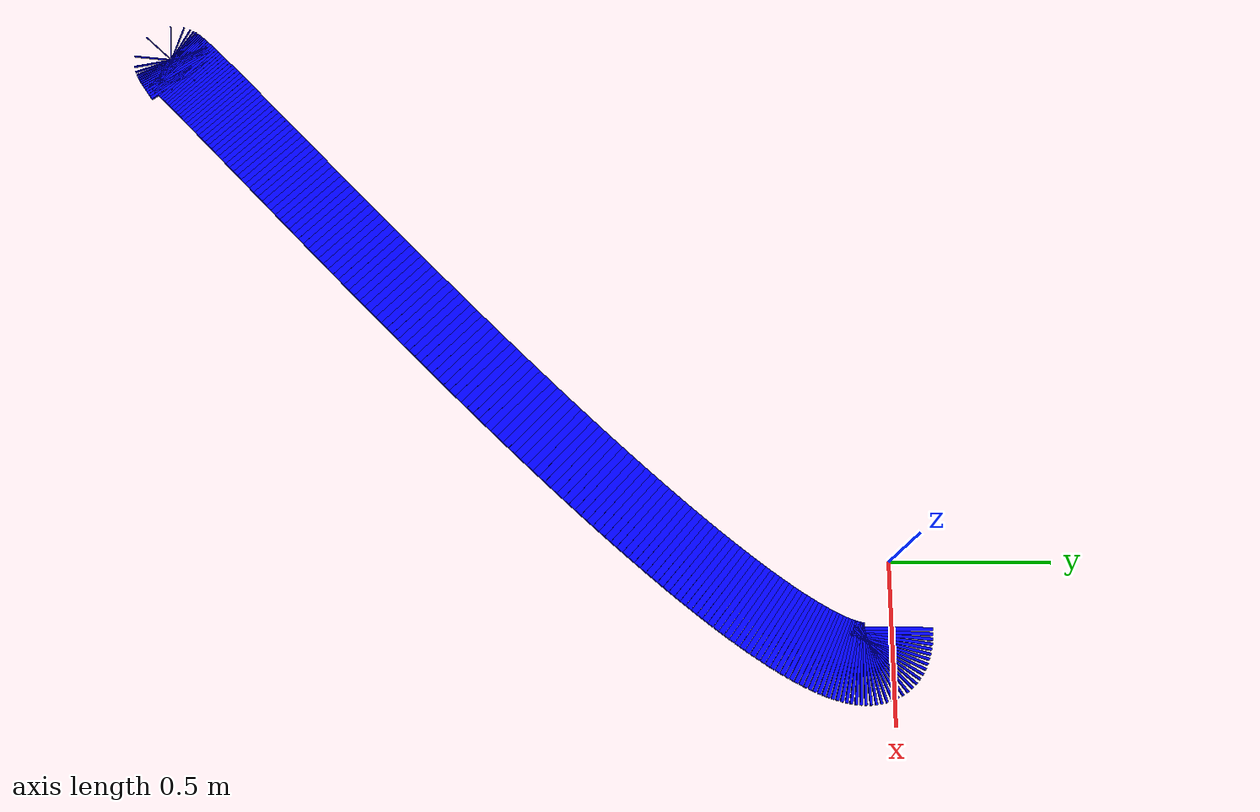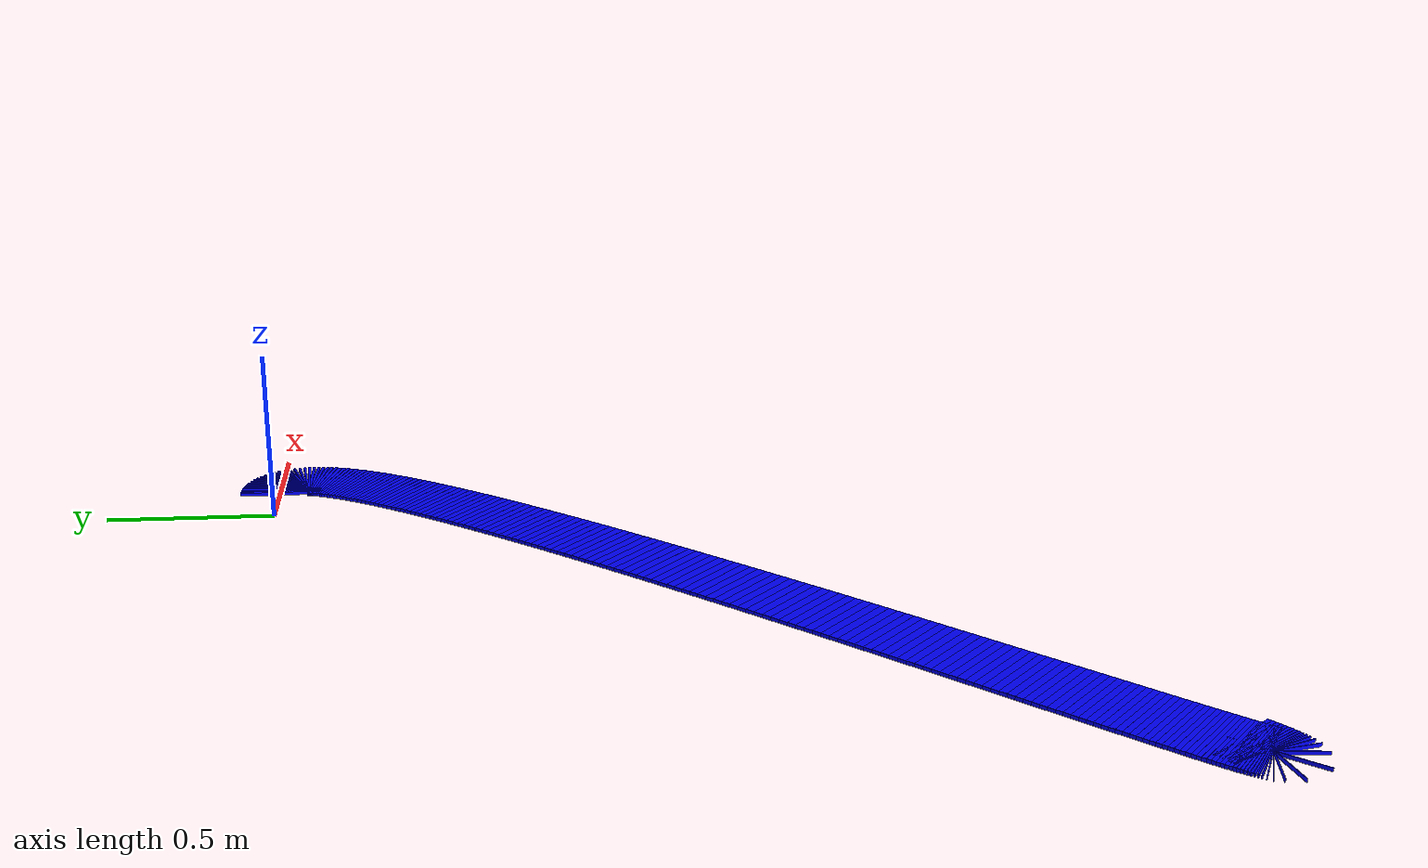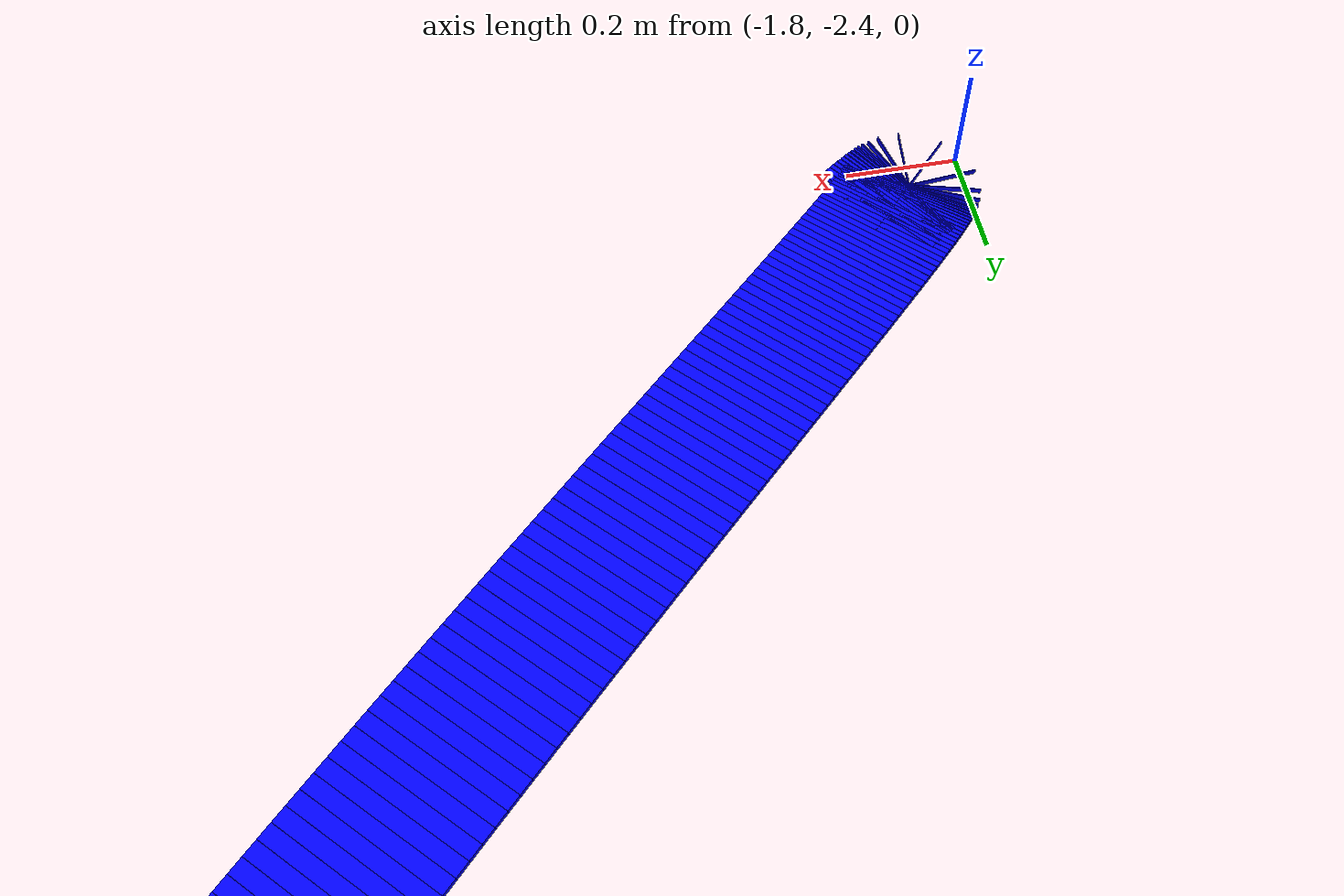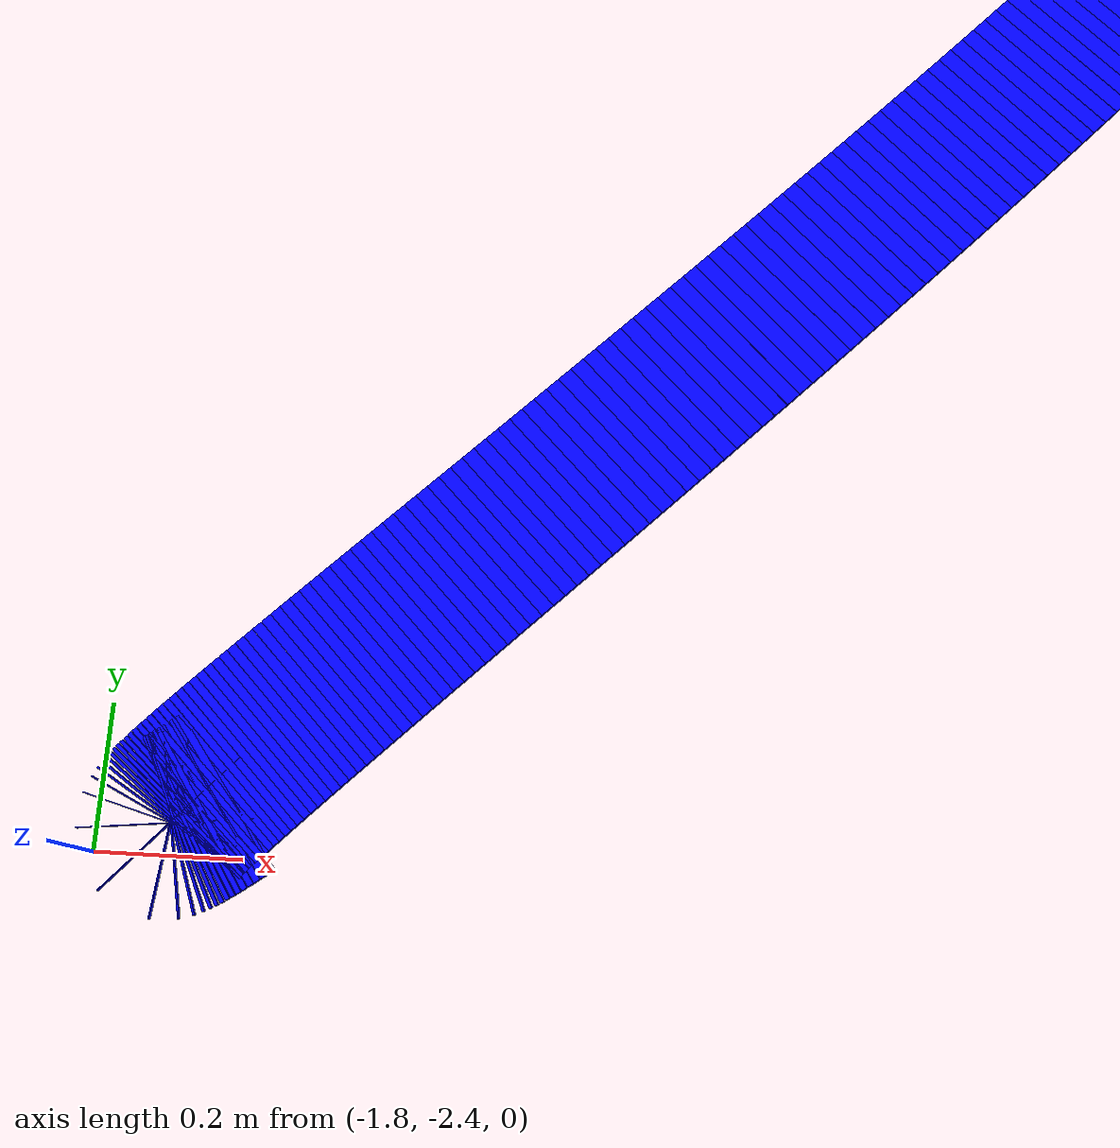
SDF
<?xml version='1.0' encoding='utf-8'?>
<sdf version="1.6"><model name="fita_curva"><static>true</static><link name="link_fita"><visual name="visual_0"><pose>0.2054064240039506 -0.0001037867309486021 0.0 0 0 0.0</pose><geometry><box><size>0.01081484021075005 0.25 0.01</size></box></geometry><material><ambient>0 0 1 1</ambient><diffuse>0 0 1 1</diffuse><specular>0 0 1 1</specular><emissive>0 0 1 1</emissive></material></visual><collision name="collision_0"><pose>0.2054064240039506 -0.0001037867309486021 0.0 0 0 0.0</pose><geometry><box><size>0.01081484021075005 0.25 0.01</size></box></geometry></collision><visual name="visual_1"><pose>0.21592715370050986 -0.0005174261638178524 0.0 0 0 -0.039371529723562594</pose><geometry><box><size>0.010247366766996693 0.25 0.01</size></box></geometry><material><ambient>0 0 1 1</ambient><diffuse>0 0 1 1</diffuse><specular>0 0 1 1</specular><emissive>0 0 1 1</emissive></material></visual><collision name="collision_1"><pose>0.21592715370050986 -0.0005174261638178524 0.0 0 0 -0.039371529723562594</pose><geometry><box><size>0.010247366766996693 0.25 0.01</size></box></geometry></collision><visual name="visual_2"><pose>0.22586655637273476 -0.0013409363022434577 0.0 0 0 -0.08274762721747744</pose><geometry><box><size>0.00970472149518541 0.25 0.01</size></box></geometry><material><ambient>0 0 1 1</ambient><diffuse>0 0 1 1</diffuse><specular>0 0 1 1</specular><emissive>0 0 1 1</emissive></material></visual><collision name="collision_2"><pose>0.22586655637273476 -0.0013409363022434577 0.0 0 0 -0.08274762721747744</pose><geometry><box><size>0.00970472149518541 0.25 0.01</size></box></geometry></collision><visual name="visual_3"><pose>0.235230451217324 -0.002569794673449945 0.0 0 0 -0.1305804914704319</pose><geometry><box><size>0.009189602480212427 0.25 0.01</size></box></geometry><material><ambient>0 0 1 1</ambient><diffuse>0 0 1 1</diffuse><specular>0 0 1 1</specular><emissive>0 0 1 1</emissive></material></visual><collision name="collision_3"><pose>0.235230451217324 -0.002569794673449945 0.0 0 0 -0.1305804914704319</pose><geometry><box><size>0.009189602480212427 0.25 0.01</size></box></geometry></collision><visual name="visual_4"><pose>0.24402465743097626 -0.004199478804661839 0.0 0 0 -0.18333739635942098</pose><geometry><box><size>0.008705120270440563 0.25 0.01</size></box></geometry><material><ambient>0 0 1 1</ambient><diffuse>0 0 1 1</diffuse><specular>0 0 1 1</specular><emissive>0 0 1 1</emissive></material></visual><collision name="collision_4"><pose>0.24402465743097626 -0.004199478804661839 0.0 0 0 -0.18333739635942098</pose><geometry><box><size>0.008705120270440563 0.25 0.01</size></box></geometry></collision><visual name="visual_5"><pose>0.25225499421039027 -0.006225466223103665 0.0 0 0 -0.24147588652323138</pose><geometry><box><size>0.008254816209906807 0.25 0.01</size></box></geometry><material><ambient>0 0 1 1</ambient><diffuse>0 0 1 1</diffuse><specular>0 0 1 1</specular><emissive>0 0 1 1</emissive></material></visual><collision name="collision_5"><pose>0.25225499421039027 -0.006225466223103665 0.0 0 0 -0.24147588652323138</pose><geometry><box><size>0.008254816209906807 0.25 0.01</size></box></geometry></collision><visual name="visual_6"><pose>0.2599272807522647 -0.00864323445599995 0.0 0 0 -0.3054047696644129</pose><geometry><box><size>0.007842648192632888 0.25 0.01</size></box></geometry><material><ambient>0 0 1 1</ambient><diffuse>0 0 1 1</diffuse><specular>0 0 1 1</specular><emissive>0 0 1 1</emissive></material></visual><collision name="collision_6"><pose>0.2599272807522647 -0.00864323445599995 0.0 0 0 -0.3054047696644129</pose><geometry><box><size>0.007842648192632888 0.25 0.01</size></box></geometry></collision><visual name="visual_7"><pose>0.26704733625329835 -0.01144826103057522 0.0 0 0 -0.37542792133118963</pose><geometry><box><size>0.007472923563068851 0.25 0.01</size></box></geometry><material><ambient>0 0 1 1</ambient><diffuse>0 0 1 1</diffuse><specular>0 0 1 1</specular><emissive>0 0 1 1</emissive></material></visual><collision name="collision_7"><pose>0.26704733625329835 -0.01144826103057522 0.0 0 0 -0.37542792133118963</pose><geometry><box><size>0.007472923563068851 0.25 0.01</size></box></geometry></collision><visual name="visual_8"><pose>0.27362097991018985 -0.014636023474053999 0.0 0 0 -0.4516705250360922</pose><geometry><box><size>0.007150156074296804 0.25 0.01</size></box></geometry><material><ambient>0 0 1 1</ambient><diffuse>0 0 1 1</diffuse><specular>0 0 1 1</specular><emissive>0 0 1 1</emissive></material></visual><collision name="collision_8"><pose>0.27362097991018985 -0.014636023474053999 0.0 0 0 -0.4516705250360922</pose><geometry><box><size>0.007150156074296804 0.25 0.01</size></box></geometry></collision><visual name="visual_9"><pose>0.27965403091963786 -0.018201999313660816 0.0 0 0 -0.5339929689648004</pose><geometry><box><size>0.006878827370967173 0.25 0.01</size></box></geometry><material><ambient>0 0 1 1</ambient><diffuse>0 0 1 1</diffuse><specular>0 0 1 1</specular><emissive>0 0 1 1</emissive></material></visual><collision name="collision_9"><pose>0.27965403091963786 -0.018201999313660816 0.0 0 0 -0.5339929689648004</pose><geometry><box><size>0.006878827370967173 0.25 0.01</size></box></geometry></collision><visual name="visual_10"><pose>0.28515230847834117 -0.022141666076620197 0.0 0 0 -0.6219064060965704</pose><geometry><box><size>0.006663048417711595 0.25 0.01</size></box></geometry><material><ambient>0 0 1 1</ambient><diffuse>0 0 1 1</diffuse><specular>0 0 1 1</specular><emissive>0 0 1 1</emissive></material></visual><collision name="collision_10"><pose>0.28515230847834117 -0.022141666076620197 0.0 0 0 -0.6219064060965704</pose><geometry><box><size>0.006663048417711595 0.25 0.01</size></box></geometry></collision><visual name="visual_11"><pose>0.29012163178299843 -0.026450501290156657 0.0 0 0 -0.7145138292012843</pose><geometry><box><size>0.006506145382042997 0.25 0.01</size></box></geometry><material><ambient>0 0 1 1</ambient><diffuse>0 0 1 1</diffuse><specular>0 0 1 1</specular><emissive>0 0 1 1</emissive></material></visual><collision name="collision_11"><pose>0.29012163178299843 -0.026450501290156657 0.0 0 0 -0.7145138292012843</pose><geometry><box><size>0.006506145382042997 0.25 0.01</size></box></geometry></collision><visual name="visual_12"><pose>0.29456782003030835 -0.03112398248149474 0.0 0 0 -0.8105058559176579</pose><geometry><box><size>0.006410232728601697 0.25 0.01</size></box></geometry><material><ambient>0 0 1 1</ambient><diffuse>0 0 1 1</diffuse><specular>0 0 1 1</specular><emissive>0 0 1 1</emissive></material></visual><collision name="collision_12"><pose>0.29456782003030835 -0.03112398248149474 0.0 0 0 -0.8105058559176579</pose><geometry><box><size>0.006410232728601697 0.25 0.01</size></box></geometry></collision><visual name="visual_13"><pose>0.2984966924169698 -0.03615758717785897 0.0 0 0 -0.9082338364636374</pose><geometry><box><size>0.006375867384758624 0.25 0.01</size></box></geometry><material><ambient>0 0 1 1</ambient><diffuse>0 0 1 1</diffuse><specular>0 0 1 1</specular><emissive>0 0 1 1</emissive></material></visual><collision name="collision_13"><pose>0.2984966924169698 -0.03615758717785897 0.0 0 0 -0.9082338364636374</pose><geometry><box><size>0.006375867384758624 0.25 0.01</size></box></geometry></collision><visual name="visual_14"><pose>0.3019140681396813 -0.04154679290647385 0.0 0 0 -1.0058609055670733</pose><geometry><box><size>0.0064018794451564335 0.25 0.01</size></box></geometry><material><ambient>0 0 1 1</ambient><diffuse>0 0 1 1</diffuse><specular>0 0 1 1</specular><emissive>0 0 1 1</emissive></material></visual><collision name="collision_14"><pose>0.3019140681396813 -0.04154679290647385 0.0 0 0 -1.0058609055670733</pose><geometry><box><size>0.0064018794451564335 0.25 0.01</size></box></geometry></collision><visual name="visual_15"><pose>0.3048257663951416 -0.04728707719456393 0.0 0 0 -1.1015613488750868</pose><geometry><box><size>0.00648543483314841 0.25 0.01</size></box></geometry><material><ambient>0 0 1 1</ambient><diffuse>0 0 1 1</diffuse><specular>0 0 1 1</specular><emissive>0 0 1 1</emissive></material></visual><collision name="collision_15"><pose>0.3048257663951416 -0.04728707719456393 0.0 0 0 -1.1015613488750868</pose><geometry><box><size>0.00648543483314841 0.25 0.01</size></box></geometry></collision><visual name="visual_16"><pose>0.30723760638004927 -0.05337391756935372 0.0 0 0 -1.1937170105007786</pose><geometry><box><size>0.006622316755509725 0.25 0.01</size></box></geometry><material><ambient>0 0 1 1</ambient><diffuse>0 0 1 1</diffuse><specular>0 0 1 1</specular><emissive>0 0 1 1</emissive></material></visual><collision name="collision_16"><pose>0.30723760638004927 -0.05337391756935372 0.0 0 0 -1.1937170105007786</pose><geometry><box><size>0.006622316755509725 0.25 0.01</size></box></geometry></collision><visual name="visual_17"><pose>0.30915540729110336 -0.05980279155806776 0.0 0 0 -1.2810608484212702</pose><geometry><box><size>0.006807349682455406 0.25 0.01</size></box></geometry><material><ambient>0 0 1 1</ambient><diffuse>0 0 1 1</diffuse><specular>0 0 1 1</specular><emissive>0 0 1 1</emissive></material></visual><collision name="collision_17"><pose>0.30915540729110336 -0.05980279155806776 0.0 0 0 -1.2810608484212702</pose><geometry><box><size>0.006807349682455406 0.25 0.01</size></box></geometry></collision><visual name="visual_18"><pose>0.3105849883250023 -0.06656917668793058 0.0 0 0 -1.3627411858300094</pose><geometry><box><size>0.007034862393798276 0.25 0.01</size></box></geometry><material><ambient>0 0 1 1</ambient><diffuse>0 0 1 1</diffuse><specular>0 0 1 1</specular><emissive>0 0 1 1</emissive></material></visual><collision name="collision_18"><pose>0.3105849883250023 -0.06656917668793058 0.0 0 0 -1.3627411858300094</pose><geometry><box><size>0.007034862393798276 0.25 0.01</size></box></geometry></collision><visual name="visual_19"><pose>0.31153216867844485 -0.07366855048616669 0.0 0 0 -1.4383102755729702</pose><geometry><box><size>0.007299100983300926 0.25 0.01</size></box></geometry><material><ambient>0 0 1 1</ambient><diffuse>0 0 1 1</diffuse><specular>0 0 1 1</specular><emissive>0 0 1 1</emissive></material></visual><collision name="collision_19"><pose>0.31153216867844485 -0.07366855048616669 0.0 0 0 -1.4383102755729702</pose><geometry><box><size>0.007299100983300926 0.25 0.01</size></box></geometry></collision><visual name="visual_20"><pose>0.31200276754812983 -0.0810963904800006 0.0 0 0 -1.5076612479670428</pose><geometry><box><size>0.007594540982909368 0.25 0.01</size></box></geometry><material><ambient>0 0 1 1</ambient><diffuse>0 0 1 1</diffuse><specular>0 0 1 1</specular><emissive>0 0 1 1</emissive></material></visual><collision name="collision_20"><pose>0.31200276754812983 -0.0810963904800006 0.0 0 0 -1.5076612479670428</pose><geometry><box><size>0.007594540982909368 0.25 0.01</size></box></geometry></collision><visual name="visual_21"><pose>0.31200260413075576 -0.08884817419665686 0.0 0 0 -1.5709425090594724</pose><geometry><box><size>0.007916086897714098 0.25 0.01</size></box></geometry><material><ambient>0 0 1 1</ambient><diffuse>0 0 1 1</diffuse><specular>0 0 1 1</specular><emissive>0 0 1 1</emissive></material></visual><collision name="collision_21"><pose>0.31200260413075576 -0.08884817419665686 0.0 0 0 -1.5709425090594724</pose><geometry><box><size>0.007916086897714098 0.25 0.01</size></box></geometry></collision><visual name="visual_22"><pose>0.31153749762302146 -0.09691937916336002 0.0 0 0 -1.6284724707082496</pose><geometry><box><size>0.008259173584262642 0.25 0.01</size></box></geometry><material><ambient>0 0 1 1</ambient><diffuse>0 0 1 1</diffuse><specular>0 0 1 1</specular><emissive>0 0 1 1</emissive></material></visual><collision name="collision_22"><pose>0.31153749762302146 -0.09691937916336002 0.0 0 0 -1.6284724707082496</pose><geometry><box><size>0.008259173584262642 0.25 0.01</size></box></geometry></collision><visual name="visual_23"><pose>0.31061326722162563 -0.10530548290733455 0.0 0 0 -1.680667558018025</pose><geometry><box><size>0.008619794907175153 0.25 0.01</size></box></geometry><material><ambient>0 0 1 1</ambient><diffuse>0 0 1 1</diffuse><specular>0 0 1 1</specular><emissive>0 0 1 1</emissive></material></visual><collision name="collision_23"><pose>0.31061326722162563 -0.10530548290733455 0.0 0 0 -1.680667558018025</pose><geometry><box><size>0.008619794907175153 0.25 0.01</size></box></geometry></collision><visual name="visual_24"><pose>0.30923573212326694 -0.114001962955805 0.0 0 0 -1.7279879498377275</pose><geometry><box><size>0.008994485390480764 0.25 0.01</size></box></geometry><material><ambient>0 0 1 1</ambient><diffuse>0 0 1 1</diffuse><specular>0 0 1 1</specular><emissive>0 0 1 1</emissive></material></visual><collision name="collision_24"><pose>0.30923573212326694 -0.114001962955805 0.0 0 0 -1.7279879498377275</pose><geometry><box><size>0.008994485390480764 0.25 0.01</size></box></geometry></collision><visual name="visual_25"><pose>0.3074107115246442 -0.12300429683599592 0.0 0 0 -1.7709002666335065</pose><geometry><box><size>0.009380275668142262 0.25 0.01</size></box></geometry><material><ambient>0 0 1 1</ambient><diffuse>0 0 1 1</diffuse><specular>0 0 1 1</specular><emissive>0 0 1 1</emissive></material></visual><collision name="collision_25"><pose>0.3074107115246442 -0.12300429683599592 0.0 0 0 -1.7709002666335065</pose><geometry><box><size>0.009380275668142262 0.25 0.01</size></box></geometry></collision><visual name="visual_26"><pose>0.30514402462245593 -0.13230796207513185 0.0 0 0 -1.8098540779446424</pose><geometry><box><size>0.009774636380493293 0.25 0.01</size></box></geometry><material><ambient>0 0 1 1</ambient><diffuse>0 0 1 1</diffuse><specular>0 0 1 1</specular><emissive>0 0 1 1</emissive></material></visual><collision name="collision_26"><pose>0.30514402462245593 -0.13230796207513185 0.0 0 0 -1.8098540779446424</pose><geometry><box><size>0.009774636380493293 0.25 0.01</size></box></geometry></collision><visual name="visual_27"><pose>0.302441490613401 -0.14190843620043725 0.0 0 0 -1.845268609212397</pose><geometry><box><size>0.010175419757080681 0.25 0.01</size></box></geometry><material><ambient>0 0 1 1</ambient><diffuse>0 0 1 1</diffuse><specular>0 0 1 1</specular><emissive>0 0 1 1</emissive></material></visual><collision name="collision_27"><pose>0.302441490613401 -0.14190843620043725 0.0 0 0 -1.845268609212397</pose><geometry><box><size>0.010175419757080681 0.25 0.01</size></box></geometry></collision><visual name="visual_28"><pose>0.2993089286941781 -0.15180119673913667 0.0 0 0 -1.8775264406250267</pose><geometry><box><size>0.010580804109453801 0.25 0.01</size></box></geometry><material><ambient>0 0 1 1</ambient><diffuse>0 0 1 1</diffuse><specular>0 0 1 1</specular><emissive>0 0 1 1</emissive></material></visual><collision name="collision_28"><pose>0.2993089286941781 -0.15180119673913667 0.0 0 0 -1.8775264406250267</pose><geometry><box><size>0.010580804109453801 0.25 0.01</size></box></geometry></collision><visual name="visual_29"><pose>0.2957521580614858 -0.16198172121845464 0.0 0 0 -1.906971703160289</pose><geometry><box><size>0.01098924377661067 0.25 0.01</size></box></geometry><material><ambient>0 0 1 1</ambient><diffuse>0 0 1 1</diffuse><specular>0 0 1 1</specular><emissive>0 0 1 1</emissive></material></visual><collision name="collision_29"><pose>0.2957521580614858 -0.16198172121845464 0.0 0 0 -1.906971703160289</pose><geometry><box><size>0.01098924377661067 0.25 0.01</size></box></geometry></collision><visual name="visual_30"><pose>0.291776997912023 -0.1724454871656157 0.0 0 0 -1.9339109815772404</pose><geometry><box><size>0.011399425422645352 0.25 0.01</size></box></geometry><material><ambient>0 0 1 1</ambient><diffuse>0 0 1 1</diffuse><specular>0 0 1 1</specular><emissive>0 0 1 1</emissive></material></visual><collision name="collision_30"><pose>0.291776997912023 -0.1724454871656157 0.0 0 0 -1.9339109815772404</pose><geometry><box><size>0.011399425422645352 0.25 0.01</size></box></geometry></collision><visual name="visual_31"><pose>0.28738926744248827 -0.18318797210784432 0.0 0 0 -1.9586157119382712</pose><geometry><box><size>0.01181023066022677 0.25 0.01</size></box></geometry><material><ambient>0 0 1 1</ambient><diffuse>0 0 1 1</diffuse><specular>0 0 1 1</specular><emissive>0 0 1 1</emissive></material></visual><collision name="collision_31"><pose>0.28738926744248827 -0.18318797210784432 0.0 0 0 -1.9586157119382712</pose><geometry><box><size>0.01181023066022677 0.25 0.01</size></box></geometry></collision><visual name="visual_32"><pose>0.28259478584958037 -0.1942046535723651 0.0 0 0 -1.9813252908057175</pose><geometry><box><size>0.012220704505537378 0.25 0.01</size></box></geometry><material><ambient>0 0 1 1</ambient><diffuse>0 0 1 1</diffuse><specular>0 0 1 1</specular><emissive>0 0 1 1</emissive></material></visual><collision name="collision_32"><pose>0.28259478584958037 -0.1942046535723651 0.0 0 0 -1.9813252908057175</pose><geometry><box><size>0.012220704505537378 0.25 0.01</size></box></geometry></collision><visual name="visual_33"><pose>0.277399372329998 -0.20549100908640255 0.0 0 0 -2.0022504133981855</pose><geometry><box><size>0.012630028976173385 0.25 0.01</size></box></geometry><material><ambient>0 0 1 1</ambient><diffuse>0 0 1 1</diffuse><specular>0 0 1 1</specular><emissive>0 0 1 1</emissive></material></visual><collision name="collision_33"><pose>0.277399372329998 -0.20549100908640255 0.0 0 0 -2.0022504133981855</pose><geometry><box><size>0.012630028976173385 0.25 0.01</size></box></geometry></collision><visual name="visual_34"><pose>0.2718088460804398 -0.2170425161771812 0.0 0 0 -2.0215763585973816</pose><geometry><box><size>0.013037501102795467 0.25 0.01</size></box></geometry><material><ambient>0 0 1 1</ambient><diffuse>0 0 1 1</diffuse><specular>0 0 1 1</specular><emissive>0 0 1 1</emissive></material></visual><collision name="collision_34"><pose>0.2718088460804398 -0.2170425161771812 0.0 0 0 -2.0215763585973816</pose><geometry><box><size>0.013037501102795467 0.25 0.01</size></box></geometry></collision><visual name="visual_35"><pose>0.2658290262976046 -0.22885465237192554 0.0 0 0 -2.0394660680449377</pose><geometry><box><size>0.013442514663612784 0.25 0.01</size></box></geometry><material><ambient>0 0 1 1</ambient><diffuse>0 0 1 1</diffuse><specular>0 0 1 1</specular><emissive>0 0 1 1</emissive></material></visual><collision name="collision_35"><pose>0.2658290262976046 -0.22885465237192554 0.0 0 0 -2.0394660680449377</pose><geometry><box><size>0.013442514663612784 0.25 0.01</size></box></geometry></collision><visual name="visual_36"><pose>0.2594657321781909 -0.24092289519786014 0.0 0 0 -2.056062947225836</pose><geometry><box><size>0.01384454502439677 0.25 0.01</size></box></geometry><material><ambient>0 0 1 1</ambient><diffuse>0 0 1 1</diffuse><specular>0 0 1 1</specular><emissive>0 0 1 1</emissive></material></visual><collision name="collision_36"><pose>0.2594657321781909 -0.24092289519786014 0.0 0 0 -2.056062947225836</pose><geometry><box><size>0.01384454502439677 0.25 0.01</size></box></geometry></collision><visual name="visual_37"><pose>0.25272478291889766 -0.2532427221822095 0.0 0 0 -2.0714933649207574</pose><geometry><box><size>0.014243136551299386 0.25 0.01</size></box></geometry><material><ambient>0 0 1 1</ambient><diffuse>0 0 1 1</diffuse><specular>0 0 1 1</specular><emissive>0 0 1 1</emissive></material></visual><collision name="collision_37"><pose>0.25272478291889766 -0.2532427221822095 0.0 0 0 -2.0714933649207574</pose><geometry><box><size>0.014243136551299386 0.25 0.01</size></box></geometry></collision><visual name="visual_38"><pose>0.2456119977164235 -0.2658096108521981 0.0 0 0 -2.08586885520777</pose><geometry><box><size>0.014637892146611143 0.25 0.01</size></box></geometry><material><ambient>0 0 1 1</ambient><diffuse>0 0 1 1</diffuse><specular>0 0 1 1</specular><emissive>0 0 1 1</emissive></material></visual><collision name="collision_38"><pose>0.2456119977164235 -0.2658096108521981 0.0 0 0 -2.08586885520777</pose><geometry><box><size>0.014637892146611143 0.25 0.01</size></box></geometry></collision><visual name="visual_39"><pose>0.23813319576746708 -0.27861903873505056 0.0 0 0 -2.099288041014772</pose><geometry><box><size>0.015028464532782662 0.25 0.01</size></box></geometry><material><ambient>0 0 1 1</ambient><diffuse>0 0 1 1</diffuse><specular>0 0 1 1</specular><emissive>0 0 1 1</emissive></material></visual><collision name="collision_39"><pose>0.23813319576746708 -0.27861903873505056 0.0 0 0 -2.099288041014772</pose><geometry><box><size>0.015028464532782662 0.25 0.01</size></box></geometry></collision><visual name="visual_40"><pose>0.23029419626872713 -0.29166648335799134 0.0 0 0 -2.111838305115784</pose><geometry><box><size>0.015414548975421851 0.25 0.01</size></box></geometry><material><ambient>0 0 1 1</ambient><diffuse>0 0 1 1</diffuse><specular>0 0 1 1</specular><emissive>0 0 1 1</emissive></material></visual><collision name="collision_40"><pose>0.23029419626872713 -0.29166648335799134 0.0 0 0 -2.111838305115784</pose><geometry><box><size>0.015414548975421851 0.25 0.01</size></box></geometry></collision><visual name="visual_41"><pose>0.22210081841690232 -0.30494742224824495 0.0 0 0 -2.123597236663802</pose><geometry><box><size>0.01579587719131934 0.25 0.01</size></box></geometry><material><ambient>0 0 1 1</ambient><diffuse>0 0 1 1</diffuse><specular>0 0 1 1</specular><emissive>0 0 1 1</emissive></material></visual><collision name="collision_41"><pose>0.22210081841690232 -0.30494742224824495 0.0 0 0 -2.123597236663802</pose><geometry><box><size>0.01579587719131934 0.25 0.01</size></box></geometry></collision><visual name="visual_42"><pose>0.2135588814086915 -0.31845733293303596 0.0 0 0 -2.134633880898552</pose><geometry><box><size>0.016172212233654858 0.25 0.01</size></box></geometry><material><ambient>0 0 1 1</ambient><diffuse>0 0 1 1</diffuse><specular>0 0 1 1</specular><emissive>0 0 1 1</emissive></material></visual><collision name="collision_42"><pose>0.2135588814086915 -0.31845733293303596 0.0 0 0 -2.134633880898552</pose><geometry><box><size>0.016172212233654858 0.25 0.01</size></box></geometry></collision><visual name="visual_43"><pose>0.20467420444079315 -0.33219169293958895 0.0 0 0 -2.145009817817615</pose><geometry><box><size>0.016543344184490615 0.25 0.01</size></box></geometry><material><ambient>0 0 1 1</ambient><diffuse>0 0 1 1</diffuse><specular>0 0 1 1</specular><emissive>0 0 1 1</emissive></material></visual><collision name="collision_43"><pose>0.20467420444079315 -0.33219169293958895 0.0 0 0 -2.145009817817615</pose><geometry><box><size>0.016543344184490615 0.25 0.01</size></box></geometry></collision><visual name="visual_44"><pose>0.1954526067099061 -0.3461459797951283 0.0 0 0 -2.154780093113578</pose><geometry><box><size>0.016909086515715335 0.25 0.01</size></box></geometry><material><ambient>0 0 1 1</ambient><diffuse>0 0 1 1</diffuse><specular>0 0 1 1</specular><emissive>0 0 1 1</emissive></material></visual><collision name="collision_44"><pose>0.1954526067099061 -0.3461459797951283 0.0 0 0 -2.154780093113578</pose><geometry><box><size>0.016909086515715335 0.25 0.01</size></box></geometry></collision><visual name="visual_45"><pose>0.1858999074127291 -0.36031567102687867 0.0 0 0 -2.1639940220028477</pose><geometry><box><size>0.01726927300490228 0.25 0.01</size></box></geometry><material><ambient>0 0 1 1</ambient><diffuse>0 0 1 1</diffuse><specular>0 0 1 1</specular><emissive>0 0 1 1</emissive></material></visual><collision name="collision_45"><pose>0.1858999074127291 -0.36031567102687867 0.0 0 0 -2.1639940220028477</pose><geometry><box><size>0.01726927300490228 0.25 0.01</size></box></geometry></collision><visual name="visual_46"><pose>0.17602192574596076 -0.3746962441620645 0.0 0 0 -2.172695883952354</pose><geometry><box><size>0.017623755113091322 0.25 0.01</size></box></geometry><material><ambient>0 0 1 1</ambient><diffuse>0 0 1 1</diffuse><specular>0 0 1 1</specular><emissive>0 0 1 1</emissive></material></visual><collision name="collision_46"><pose>0.17602192574596076 -0.3746962441620645 0.0 0 0 -2.172695883952354</pose><geometry><box><size>0.017623755113091322 0.25 0.01</size></box></geometry></collision><visual name="visual_47"><pose>0.16582448090629986 -0.38928317672791035 0.0 0 0 -2.180925523877644</pose><geometry><box><size>0.017972399748223452 0.25 0.01</size></box></geometry><material><ambient>0 0 1 1</ambient><diffuse>0 0 1 1</diffuse><specular>0 0 1 1</specular><emissive>0 0 1 1</emissive></material></visual><collision name="collision_47"><pose>0.16582448090629986 -0.38928317672791035 0.0 0 0 -2.180925523877644</pose><geometry><box><size>0.017972399748223452 0.25 0.01</size></box></geometry></collision><visual name="visual_48"><pose>0.1553133920904451 -0.4040719462516408 0.0 0 0 -2.1887188731970775</pose><geometry><box><size>0.018315087351491444 0.25 0.01</size></box></geometry><material><ambient>0 0 1 1</ambient><diffuse>0 0 1 1</diffuse><specular>0 0 1 1</specular><emissive>0 0 1 1</emissive></material></visual><collision name="collision_48"><pose>0.1553133920904451 -0.4040719462516408 0.0 0 0 -2.1887188731970775</pose><geometry><box><size>0.018315087351491444 0.25 0.01</size></box></geometry></collision><visual name="visual_49"><pose>0.14449447849509517 -0.4190580302604802 0.0 0 0 -2.1961084021976</pose><geometry><box><size>0.018651710254914477 0.25 0.01</size></box></geometry><material><ambient>0 0 1 1</ambient><diffuse>0 0 1 1</diffuse><specular>0 0 1 1</specular><emissive>0 0 1 1</emissive></material></visual><collision name="collision_49"><pose>0.14449447849509517 -0.4190580302604802 0.0 0 0 -2.1961084021976</pose><geometry><box><size>0.018651710254914477 0.25 0.01</size></box></geometry></collision><visual name="visual_50"><pose>0.13337355931694883 -0.4342369062816533 0.0 0 0 -2.2031235134904366</pose><geometry><box><size>0.018982171267401877 0.25 0.01</size></box></geometry><material><ambient>0 0 1 1</ambient><diffuse>0 0 1 1</diffuse><specular>0 0 1 1</specular><emissive>0 0 1 1</emissive></material></visual><collision name="collision_50"><pose>0.13337355931694883 -0.4342369062816533 0.0 0 0 -2.2031235134904366</pose><geometry><box><size>0.018982171267401877 0.25 0.01</size></box></geometry></collision><visual name="visual_51"><pose>0.12195645375270464 -0.44960405184238456 0.0 0 0 -2.2097908848907606</pose><geometry><box><size>0.01930638245389744 0.25 0.01</size></box></geometry><material><ambient>0 0 1 1</ambient><diffuse>0 0 1 1</diffuse><specular>0 0 1 1</specular><emissive>0 0 1 1</emissive></material></visual><collision name="collision_51"><pose>0.12195645375270464 -0.44960405184238456 0.0 0 0 -2.2097908848907606</pose><geometry><box><size>0.01930638245389744 0.25 0.01</size></box></geometry></collision><visual name="visual_52"><pose>0.11024898099906145 -0.46515494446989836 0.0 0 0 -2.216134768819591</pose><geometry><box><size>0.01962426407817647 0.25 0.01</size></box></geometry><material><ambient>0 0 1 1</ambient><diffuse>0 0 1 1</diffuse><specular>0 0 1 1</specular><emissive>0 0 1 1</emissive></material></visual><collision name="collision_52"><pose>0.11024898099906145 -0.46515494446989836 0.0 0 0 -2.216134768819591</pose><geometry><box><size>0.01962426407817647 0.25 0.01</size></box></geometry></collision><visual name="visual_53"><pose>0.0982569602527178 -0.4808850616914194 0.0 0 0 -2.2221772542734324</pose><geometry><box><size>0.019935743684763974 0.25 0.01</size></box></geometry><material><ambient>0 0 1 1</ambient><diffuse>0 0 1 1</diffuse><specular>0 0 1 1</specular><emissive>0 0 1 1</emissive></material></visual><collision name="collision_53"><pose>0.0982569602527178 -0.4808850616914194 0.0 0 0 -2.2221772542734324</pose><geometry><box><size>0.019935743684763974 0.25 0.01</size></box></geometry></collision><visual name="visual_54"><pose>0.08598621071037249 -0.4967898810341722 0.0 0 0 -2.2279384965128415</pose><geometry><box><size>0.02024075529946488 0.25 0.01</size></box></geometry><material><ambient>0 0 1 1</ambient><diffuse>0 0 1 1</diffuse><specular>0 0 1 1</specular><emissive>0 0 1 1</emissive></material></visual><collision name="collision_54"><pose>0.08598621071037249 -0.4967898810341722 0.0 0 0 -2.2279384965128415</pose><geometry><box><size>0.02024075529946488 0.25 0.01</size></box></geometry></collision><visual name="visual_55"><pose>0.07344255156872441 -0.5128648800253812 0.0 0 0 -2.233436918862709</pose><geometry><box><size>0.020539238731326886 0.25 0.01</size></box></geometry><material><ambient>0 0 1 1</ambient><diffuse>0 0 1 1</diffuse><specular>0 0 1 1</specular><emissive>0 0 1 1</emissive></material></visual><collision name="collision_55"><pose>0.07344255156872441 -0.5128648800253812 0.0 0 0 -2.233436918862709</pose><geometry><box><size>0.020539238731326886 0.25 0.01</size></box></geometry></collision><visual name="visual_56"><pose>0.06063180202447198 -0.5291055361922709 0.0 0 0 -2.2386893903744856</pose><geometry><box><size>0.020831138961566905 0.25 0.01</size></box></geometry><material><ambient>0 0 1 1</ambient><diffuse>0 0 1 1</diffuse><specular>0 0 1 1</specular><emissive>0 0 1 1</emissive></material></visual><collision name="collision_56"><pose>0.06063180202447198 -0.5291055361922709 0.0 0 0 -2.2386893903744856</pose><geometry><box><size>0.020831138961566905 0.25 0.01</size></box></geometry></collision><visual name="visual_57"><pose>0.047559781274314095 -0.5455073270620658 0.0 0 0 -2.2437113825562305</pose><geometry><box><size>0.02111640560728309 0.25 0.01</size></box></geometry><material><ambient>0 0 1 1</ambient><diffuse>0 0 1 1</diffuse><specular>0 0 1 1</specular><emissive>0 0 1 1</emissive></material></visual><collision name="collision_57"><pose>0.047559781274314095 -0.5455073270620658 0.0 0 0 -2.2437113825562305</pose><geometry><box><size>0.02111640560728309 0.25 0.01</size></box></geometry></collision><visual name="visual_58"><pose>0.03423230851494942 -0.5620657301619906 0.0 0 0 -2.2485171079151787</pose><geometry><box><size>0.021394992449645503 0.25 0.01</size></box></geometry><material><ambient>0 0 1 1</ambient><diffuse>0 0 1 1</diffuse><specular>0 0 1 1</specular><emissive>0 0 1 1</emissive></material></visual><collision name="collision_58"><pose>0.03423230851494942 -0.5620657301619906 0.0 0 0 -2.2485171079151787</pose><geometry><box><size>0.021394992449645503 0.25 0.01</size></box></geometry></collision><visual name="visual_59"><pose>0.02065520294307651 -0.5787762230192698 0.0 0 0 -2.253119642666467</pose><geometry><box><size>0.02166685701781838 0.25 0.01</size></box></geometry><material><ambient>0 0 1 1</ambient><diffuse>0 0 1 1</diffuse><specular>0 0 1 1</specular><emissive>0 0 1 1</emissive></material></visual><collision name="collision_59"><pose>0.02065520294307651 -0.5787762230192698 0.0 0 0 -2.253119642666467</pose><geometry><box><size>0.02166685701781838 0.25 0.01</size></box></geometry></collision><visual name="visual_60"><pose>0.00683428375539432 -0.5956342831611278 0.0 0 0 -2.2575310356297966</pose><geometry><box><size>0.021931960221191666 0.25 0.01</size></box></geometry><material><ambient>0 0 1 1</ambient><diffuse>0 0 1 1</diffuse><specular>0 0 1 1</specular><emissive>0 0 1 1</emissive></material></visual><collision name="collision_60"><pose>0.00683428375539432 -0.5956342831611278 0.0 0 0 -2.2575310356297966</pose><geometry><box><size>0.021931960221191666 0.25 0.01</size></box></geometry></collision><visual name="visual_61"><pose>-0.007224629851398542 -0.612635388114789 0.0 0 0 -2.2617624050538625</pose><geometry><box><size>0.022190266023584242 0.25 0.01</size></box></geometry><material><ambient>0 0 1 1</ambient><diffuse>0 0 1 1</diffuse><specular>0 0 1 1</specular><emissive>0 0 1 1</emissive></material></visual><collision name="collision_61"><pose>-0.007224629851398542 -0.612635388114789 0.0 0 0 -2.2617624050538625</pose><geometry><box><size>0.022190266023584242 0.25 0.01</size></box></geometry></collision><visual name="visual_62"><pose>-0.02151571868060343 -0.6297750154074782 0.0 0 0 -2.265824024868463</pose><geometry><box><size>0.022441741153993375 0.25 0.01</size></box></geometry><material><ambient>0 0 1 1</ambient><diffuse>0 0 1 1</diffuse><specular>0 0 1 1</specular><emissive>0 0 1 1</emissive></material></visual><collision name="collision_62"><pose>-0.02151571868060343 -0.6297750154074782 0.0 0 0 -2.265824024868463</pose><geometry><box><size>0.022441741153993375 0.25 0.01</size></box></geometry></collision><visual name="visual_63"><pose>-0.0360331635355217 -0.6470486425664199 0.0 0 0 -2.2697254016598065</pose><geometry><box><size>0.02268635484926676 0.25 0.01</size></box></geometry><material><ambient>0 0 1 1</ambient><diffuse>0 0 1 1</diffuse><specular>0 0 1 1</specular><emissive>0 0 1 1</emissive></material></visual><collision name="collision_63"><pose>-0.0360331635355217 -0.6470486425664199 0.0 0 0 -2.2697254016598065</pose><geometry><box><size>0.02268635484926676 0.25 0.01</size></box></geometry></collision><visual name="visual_64"><pose>-0.05077114521945454 -0.6644517471188387 0.0 0 0 -2.27347534349009</pose><geometry><box><size>0.022924078624689558 0.25 0.01</size></box></geometry><material><ambient>0 0 1 1</ambient><diffuse>0 0 1 1</diffuse><specular>0 0 1 1</specular><emissive>0 0 1 1</emissive></material></visual><collision name="collision_64"><pose>-0.05077114521945454 -0.6644517471188387 0.0 0 0 -2.27347534349009</pose><geometry><box><size>0.022924078624689558 0.25 0.01</size></box></geometry></collision><visual name="visual_65"><pose>-0.06572384453570312 -0.6819798065919589 0.0 0 0 -2.2770820215332885</pose><geometry><box><size>0.023154886069067963 0.25 0.01</size></box></geometry><material><ambient>0 0 1 1</ambient><diffuse>0 0 1 1</diffuse><specular>0 0 1 1</specular><emissive>0 0 1 1</emissive></material></visual><collision name="collision_65"><pose>-0.06572384453570312 -0.6819798065919589 0.0 0 0 -2.2770820215332885</pose><geometry><box><size>0.023154886069067963 0.25 0.01</size></box></geometry></collision><visual name="visual_66"><pose>-0.080885442287569 -0.6996282985130049 0.0 0 0 -2.2805530253714026</pose><geometry><box><size>0.023378752661334715 0.25 0.01</size></box></geometry><material><ambient>0 0 1 1</ambient><diffuse>0 0 1 1</diffuse><specular>0 0 1 1</specular><emissive>0 0 1 1</emissive></material></visual><collision name="collision_66"><pose>-0.080885442287569 -0.6996282985130049 0.0 0 0 -2.2805530253714026</pose><geometry><box><size>0.023378752661334715 0.25 0.01</size></box></geometry></collision><visual name="visual_67"><pose>-0.09625011927835328 -0.7173927004092016 0.0 0 0 -2.2838954126858644</pose><geometry><box><size>0.023595655606107144 0.25 0.01</size></box></geometry><material><ambient>0 0 1 1</ambient><diffuse>0 0 1 1</diffuse><specular>0 0 1 1</specular><emissive>0 0 1 1</emissive></material></visual><collision name="collision_67"><pose>-0.09625011927835328 -0.7173927004092016 0.0 0 0 -2.2838954126858644</pose><geometry><box><size>0.023595655606107144 0.25 0.01</size></box></geometry></collision><visual name="visual_68"><pose>-0.11181205631135727 -0.7352684898077733 0.0 0 0 -2.2871157539846534</pose><geometry><box><size>0.023805573685987985 0.25 0.01</size></box></geometry><material><ambient>0 0 1 1</ambient><diffuse>0 0 1 1</diffuse><specular>0 0 1 1</specular><emissive>0 0 1 1</emissive></material></visual><collision name="collision_68"><pose>-0.11181205631135727 -0.7352684898077733 0.0 0 0 -2.2871157539846534</pose><geometry><box><size>0.023805573685987985 0.25 0.01</size></box></geometry></collision><visual name="visual_69"><pose>-0.12756543418988237 -0.7532511442359446 0.0 0 0 -2.2902201729246343</pose><geometry><box><size>0.024008487128651494 0.25 0.01</size></box></geometry><material><ambient>0 0 1 1</ambient><diffuse>0 0 1 1</diffuse><specular>0 0 1 1</specular><emissive>0 0 1 1</emissive></material></visual><collision name="collision_69"><pose>-0.12756543418988237 -0.7532511442359446 0.0 0 0 -2.2902201729246343</pose><geometry><box><size>0.024008487128651494 0.25 0.01</size></box></geometry></collision><visual name="visual_70"><pose>-0.14350443371722973 -0.7713361412209402 0.0 0 0 -2.2932143827186957</pose><geometry><box><size>0.02420437748704915 0.25 0.01</size></box></geometry><material><ambient>0 0 1 1</ambient><diffuse>0 0 1 1</diffuse><specular>0 0 1 1</specular><emissive>0 0 1 1</emissive></material></visual><collision name="collision_70"><pose>-0.14350443371722973 -0.7713361412209402 0.0 0 0 -2.2932143827186957</pose><geometry><box><size>0.02420437748704915 0.25 0.01</size></box></geometry></collision><visual name="visual_71"><pose>-0.1596232356967008 -0.7895189582899843 0.0 0 0 -2.296103719056899</pose><geometry><box><size>0.024393227531251692 0.25 0.01</size></box></geometry><material><ambient>0 0 1 1</ambient><diffuse>0 0 1 1</diffuse><specular>0 0 1 1</specular><emissive>0 0 1 1</emissive></material></visual><collision name="collision_71"><pose>-0.1596232356967008 -0.7895189582899843 0.0 0 0 -2.296103719056899</pose><geometry><box><size>0.024393227531251692 0.25 0.01</size></box></geometry></collision><visual name="visual_72"><pose>-0.1759160209315967 -0.8077950729703016 0.0 0 0 -2.2988931699185047</pose><geometry><box><size>0.024575021150642612 0.25 0.01</size></box></geometry><material><ambient>0 0 1 1</ambient><diffuse>0 0 1 1</diffuse><specular>0 0 1 1</specular><emissive>0 0 1 1</emissive></material></visual><collision name="collision_72"><pose>-0.1759160209315967 -0.8077950729703016 0.0 0 0 -2.2988931699185047</pose><geometry><box><size>0.024575021150642612 0.25 0.01</size></box></geometry></collision><visual name="visual_73"><pose>-0.19237697022521888 -0.8261599627891164 0.0 0 0 -2.3015874026064504</pose><geometry><box><size>0.02474974326534022 0.25 0.01</size></box></geometry><material><ambient>0 0 1 1</ambient><diffuse>0 0 1 1</diffuse><specular>0 0 1 1</specular><emissive>0 0 1 1</emissive></material></visual><collision name="collision_73"><pose>-0.19237697022521888 -0.8261599627891164 0.0 0 0 -2.3015874026064504</pose><geometry><box><size>0.02474974326534022 0.25 0.01</size></box></geometry></collision><visual name="visual_74"><pose>-0.20900026438086872 -0.8446091052736536 0.0 0 0 -2.3041907882963972</pose><geometry><box><size>0.024917379745845607 0.25 0.01</size></box></geometry><material><ambient>0 0 1 1</ambient><diffuse>0 0 1 1</diffuse><specular>0 0 1 1</specular><emissive>0 0 1 1</emissive></material></visual><collision name="collision_74"><pose>-0.20900026438086872 -0.8446091052736536 0.0 0 0 -2.3041907882963972</pose><geometry><box><size>0.024917379745845607 0.25 0.01</size></box></geometry></collision><visual name="visual_75"><pose>-0.2257800842018472 -0.8631379779511377 0.0 0 0 -2.3067074243582195</pose><geometry><box><size>0.02507791734005817 0.25 0.01</size></box></geometry><material><ambient>0 0 1 1</ambient><diffuse>0 0 1 1</diffuse><specular>0 0 1 1</specular><emissive>0 0 1 1</emissive></material></visual><collision name="collision_75"><pose>-0.2257800842018472 -0.8631379779511377 0.0 0 0 -2.3067074243582195</pose><geometry><box><size>0.02507791734005817 0.25 0.01</size></box></geometry></collision><visual name="visual_76"><pose>-0.24271061049145579 -0.8817420583487928 0.0 0 0 -2.309141154677887</pose><geometry><box><size>0.025231343606880688 0.25 0.01</size></box></geometry><material><ambient>0 0 1 1</ambient><diffuse>0 0 1 1</diffuse><specular>0 0 1 1</specular><emissive>0 0 1 1</emissive></material></visual><collision name="collision_76"><pose>-0.24271061049145579 -0.8817420583487928 0.0 0 0 -2.309141154677887</pose><geometry><box><size>0.025231343606880688 0.25 0.01</size></box></geometry></collision><visual name="visual_77"><pose>-0.25978602405299583 -0.9004168239938439 0.0 0 0 -2.311495588181577</pose><geometry><box><size>0.02537764685573644 0.25 0.01</size></box></geometry><material><ambient>0 0 1 1</ambient><diffuse>0 0 1 1</diffuse><specular>0 0 1 1</specular><emissive>0 0 1 1</emissive></material></visual><collision name="collision_77"><pose>-0.25978602405299583 -0.9004168239938439 0.0 0 0 -2.311495588181577</pose><geometry><box><size>0.02537764685573644 0.25 0.01</size></box></geometry></collision><visual name="visual_78"><pose>-0.2770005056897684 -0.919157752413515 0.0 0 0 -2.3137741157410336</pose><geometry><box><size>0.025516816091399035 0.25 0.01</size></box></geometry><material><ambient>0 0 1 1</ambient><diffuse>0 0 1 1</diffuse><specular>0 0 1 1</specular><emissive>0 0 1 1</emissive></material></visual><collision name="collision_78"><pose>-0.2770005056897684 -0.919157752413515 0.0 0 0 -2.3137741157410336</pose><geometry><box><size>0.025516816091399035 0.25 0.01</size></box></geometry></collision><visual name="visual_79"><pose>-0.294348236205075 -0.9379603211350311 0.0 0 0 -2.315979925619127</pose><geometry><box><size>0.02564884096360837 0.25 0.01</size></box></geometry><material><ambient>0 0 1 1</ambient><diffuse>0 0 1 1</diffuse><specular>0 0 1 1</specular><emissive>0 0 1 1</emissive></material></visual><collision name="collision_79"><pose>-0.294348236205075 -0.9379603211350311 0.0 0 0 -2.315979925619127</pose><geometry><box><size>0.02564884096360837 0.25 0.01</size></box></geometry></collision><visual name="visual_80"><pose>-0.3118233964022169 -0.9568200076856168 0.0 0 0 -2.3181160175970286</pose><geometry><box><size>0.02577371172098083 0.25 0.01</size></box></geometry><material><ambient>0 0 1 1</ambient><diffuse>0 0 1 1</diffuse><specular>0 0 1 1</specular><emissive>0 0 1 1</emissive></material></visual><collision name="collision_80"><pose>-0.3118233964022169 -0.9568200076856168 0.0 0 0 -2.3181160175970286</pose><geometry><box><size>0.02577371172098083 0.25 0.01</size></box></geometry></collision><visual name="visual_81"><pose>-0.3294201670844954 -0.9757322895924961 0.0 0 0 -2.3201852159089342</pose><geometry><box><size>0.025891419168824936 0.25 0.01</size></box></geometry><material><ambient>0 0 1 1</ambient><diffuse>0 0 1 1</diffuse><specular>0 0 1 1</specular><emissive>0 0 1 1</emissive></material></visual><collision name="collision_81"><pose>-0.3294201670844954 -0.9757322895924961 0.0 0 0 -2.3201852159089342</pose><geometry><box><size>0.025891419168824936 0.25 0.01</size></box></geometry></collision><visual name="visual_82"><pose>-0.34713272905521186 -0.9946926443828941 0.0 0 0 -2.3221901810966594</pose><geometry><box><size>0.026001954630453523 0.25 0.01</size></box></geometry><material><ambient>0 0 1 1</ambient><diffuse>0 0 1 1</diffuse><specular>0 0 1 1</specular><emissive>0 0 1 1</emissive></material></visual><collision name="collision_82"><pose>-0.34713272905521186 -0.9946926443828941 0.0 0 0 -2.3221901810966594</pose><geometry><box><size>0.026001954630453523 0.25 0.01</size></box></geometry></collision><visual name="visual_83"><pose>-0.36495526311766735 -1.0136965495840347 0.0 0 0 -2.324133420884423</pose><geometry><box><size>0.026105309911686567 0.25 0.01</size></box></geometry><material><ambient>0 0 1 1</ambient><diffuse>0 0 1 1</diffuse><specular>0 0 1 1</specular><emissive>0 0 1 1</emissive></material></visual><collision name="collision_83"><pose>-0.36495526311766735 -1.0136965495840347 0.0 0 0 -2.324133420884423</pose><geometry><box><size>0.026105309911686567 0.25 0.01</size></box></geometry></collision><visual name="visual_84"><pose>-0.38288195007516335 -1.032739482723143 0.0 0 0 -2.326017300163508</pose><geometry><box><size>0.02620147726823313 0.25 0.01</size></box></geometry><material><ambient>0 0 1 1</ambient><diffuse>0 0 1 1</diffuse><specular>0 0 1 1</specular><emissive>0 0 1 1</emissive></material></visual><collision name="collision_84"><pose>-0.38288195007516335 -1.032739482723143 0.0 0 0 -2.326017300163508</pose><geometry><box><size>0.02620147726823313 0.25 0.01</size></box></geometry></collision><visual name="visual_85"><pose>-0.400906970731001 -1.0518169213274433 0.0 0 0 -2.327844050167095</pose><geometry><box><size>0.026290449375681733 0.25 0.01</size></box></geometry><material><ambient>0 0 1 1</ambient><diffuse>0 0 1 1</diffuse><specular>0 0 1 1</specular><emissive>0 0 1 1</emissive></material></visual><collision name="collision_85"><pose>-0.400906970731001 -1.0518169213274433 0.0 0 0 -2.327844050167095</pose><geometry><box><size>0.026290449375681733 0.25 0.01</size></box></geometry></collision><visual name="visual_86"><pose>-0.41902450588848167 -1.0709243429241602 0.0 0 0 -2.329615776907237</pose><geometry><box><size>0.026372219301879024 0.25 0.01</size></box></geometry><material><ambient>0 0 1 1</ambient><diffuse>0 0 1 1</diffuse><specular>0 0 1 1</specular><emissive>0 0 1 1</emissive></material></visual><collision name="collision_86"><pose>-0.41902450588848167 -1.0709243429241602 0.0 0 0 -2.329615776907237</pose><geometry><box><size>0.026372219301879024 0.25 0.01</size></box></geometry></collision><visual name="visual_87"><pose>-0.4372287363509068 -1.090057225040518 0.0 0 0 -2.3313344689385214</pose><geometry><box><size>0.026446780481456638 0.25 0.01</size></box></geometry><material><ambient>0 0 1 1</ambient><diffuse>0 0 1 1</diffuse><specular>0 0 1 1</specular><emissive>0 0 1 1</emissive></material></visual><collision name="collision_87"><pose>-0.4372287363509068 -1.090057225040518 0.0 0 0 -2.3313344689385214</pose><geometry><box><size>0.026446780481456638 0.25 0.01</size></box></geometry></collision><visual name="visual_88"><pose>-0.4555138429215774 -1.1092110452037414 0.0 0 0 -2.333002004506401</pose><geometry><box><size>0.02651412669233828 0.25 0.01</size></box></geometry><material><ambient>0 0 1 1</ambient><diffuse>0 0 1 1</diffuse><specular>0 0 1 1</specular><emissive>0 0 1 1</emissive></material></visual><collision name="collision_88"><pose>-0.4555138429215774 -1.1092110452037414 0.0 0 0 -2.333002004506401</pose><geometry><box><size>0.02651412669233828 0.25 0.01</size></box></geometry></collision><visual name="visual_89"><pose>-0.473874006403795 -1.128381280941055 0.0 0 0 -2.3346201581323</pose><geometry><box><size>0.026574252034037293 0.25 0.01</size></box></geometry><material><ambient>0 0 1 1</ambient><diffuse>0 0 1 1</diffuse><specular>0 0 1 1</specular><emissive>0 0 1 1</emissive></material></visual><collision name="collision_89"><pose>-0.473874006403795 -1.128381280941055 0.0 0 0 -2.3346201581323</pose><geometry><box><size>0.026574252034037293 0.25 0.01</size></box></geometry></collision><visual name="visual_90"><pose>-0.4923034076008608 -1.1475634097796832 0.0 0 0 -2.3361906066823397</pose><geometry><box><size>0.02662715090759204 0.25 0.01</size></box></geometry><material><ambient>0 0 1 1</ambient><diffuse>0 0 1 1</diffuse><specular>0 0 1 1</specular><emissive>0 0 1 1</emissive></material></visual><collision name="collision_90"><pose>-0.4923034076008608 -1.1475634097796832 0.0 0 0 -2.3361906066823397</pose><geometry><box><size>0.02662715090759204 0.25 0.01</size></box></geometry></collision><visual name="visual_91"><pose>-0.510796227316076 -1.1667529092468505 0.0 0 0 -2.3377149349618764</pose><geometry><box><size>0.026672817997011298 0.25 0.01</size></box></geometry><material><ambient>0 0 1 1</ambient><diffuse>0 0 1 1</diffuse><specular>0 0 1 1</specular><emissive>0 0 1 1</emissive></material></visual><collision name="collision_91"><pose>-0.510796227316076 -1.1667529092468505 0.0 0 0 -2.3377149349618764</pose><geometry><box><size>0.026672817997011298 0.25 0.01</size></box></geometry></collision><visual name="visual_92"><pose>-0.5293466463527423 -1.1859452568697817 0.0 0 0 -2.339194640873807</pose><geometry><box><size>0.026711248252077848 0.25 0.01</size></box></geometry><material><ambient>0 0 1 1</ambient><diffuse>0 0 1 1</diffuse><specular>0 0 1 1</specular><emissive>0 0 1 1</emissive></material></visual><collision name="collision_92"><pose>-0.5293466463527423 -1.1859452568697817 0.0 0 0 -2.339194640873807</pose><geometry><box><size>0.026711248252077848 0.25 0.01</size></box></geometry></collision><visual name="visual_93"><pose>-0.5479488455141606 -1.2051359301757008 0.0 0 0 -2.3406311401748443</pose><geometry><box><size>0.026742436872422424 0.25 0.01</size></box></geometry><material><ambient>0 0 1 1</ambient><diffuse>0 0 1 1</diffuse><specular>0 0 1 1</specular><emissive>0 0 1 1</emissive></material></visual><collision name="collision_93"><pose>-0.5479488455141606 -1.2051359301757008 0.0 0 0 -2.3406311401748443</pose><geometry><box><size>0.026742436872422424 0.25 0.01</size></box></geometry></collision><visual name="visual_94"><pose>-0.566597005603632 -1.2243204066918327 0.0 0 0 -2.3420257708605594</pose><geometry><box><size>0.02676637929274818 0.25 0.01</size></box></geometry><material><ambient>0 0 1 1</ambient><diffuse>0 0 1 1</diffuse><specular>0 0 1 1</specular><emissive>0 0 1 1</emissive></material></visual><collision name="collision_94"><pose>-0.566597005603632 -1.2243204066918327 0.0 0 0 -2.3420257708605594</pose><geometry><box><size>0.02676637929274818 0.25 0.01</size></box></geometry></collision><visual name="visual_95"><pose>-0.5852853074244583 -1.2434941639454018 0.0 0 0 -2.3433797972069175</pose><geometry><box><size>0.026783071169107314 0.25 0.01</size></box></geometry><material><ambient>0 0 1 1</ambient><diffuse>0 0 1 1</diffuse><specular>0 0 1 1</specular><emissive>0 0 1 1</emissive></material></visual><collision name="collision_95"><pose>-0.5852853074244583 -1.2434941639454018 0.0 0 0 -2.3433797972069175</pose><geometry><box><size>0.026783071169107314 0.25 0.01</size></box></geometry></collision><visual name="visual_96"><pose>-0.6040079317799405 -1.2626526794636326 0.0 0 0 -2.3446944134932743</pose><geometry><box><size>0.026792508366172092 0.25 0.01</size></box></geometry><material><ambient>0 0 1 1</ambient><diffuse>0 0 1 1</diffuse><specular>0 0 1 1</specular><emissive>0 0 1 1</emissive></material></visual><collision name="collision_96"><pose>-0.6040079317799405 -1.2626526794636326 0.0 0 0 -2.3446944134932743</pose><geometry><box><size>0.026792508366172092 0.25 0.01</size></box></geometry></collision><visual name="visual_97"><pose>-0.6227590594733802 -1.2817914307737504 0.0 0 0 -2.3459707474292677</pose><geometry><box><size>0.026794686945379315 0.25 0.01</size></box></geometry><material><ambient>0 0 1 1</ambient><diffuse>0 0 1 1</diffuse><specular>0 0 1 1</specular><emissive>0 0 1 1</emissive></material></visual><collision name="collision_97"><pose>-0.6227590594733802 -1.2817914307737504 0.0 0 0 -2.3459707474292677</pose><geometry><box><size>0.026794686945379315 0.25 0.01</size></box></geometry></collision><visual name="visual_98"><pose>-0.6415328713080782 -1.3009058954029784 0.0 0 0 -2.347209863305753</pose><geometry><box><size>0.026789603153922748 0.25 0.01</size></box></geometry><material><ambient>0 0 1 1</ambient><diffuse>0 0 1 1</diffuse><specular>0 0 1 1</specular><emissive>0 0 1 1</emissive></material></visual><collision name="collision_98"><pose>-0.6415328713080782 -1.3009058954029784 0.0 0 0 -2.347209863305753</pose><geometry><box><size>0.026789603153922748 0.25 0.01</size></box></geometry></collision><visual name="visual_99"><pose>-0.6603235480873358 -1.3199915508785416 0.0 0 0 -2.3484127648878483</pose><geometry><box><size>0.026777253414504574 0.25 0.01</size></box></geometry><material><ambient>0 0 1 1</ambient><diffuse>0 0 1 1</diffuse><specular>0 0 1 1</specular><emissive>0 0 1 1</emissive></material></visual><collision name="collision_99"><pose>-0.6603235480873358 -1.3199915508785416 0.0 0 0 -2.3484127648878483</pose><geometry><box><size>0.026777253414504574 0.25 0.01</size></box></geometry></collision><visual name="visual_100"><pose>-0.6791252706144548 -1.339043874727665 0.0 0 0 -2.3495803980662178</pose><geometry><box><size>0.026757634315781768 0.25 0.01</size></box></geometry><material><ambient>0 0 1 1</ambient><diffuse>0 0 1 1</diffuse><specular>0 0 1 1</specular><emissive>0 0 1 1</emissive></material></visual><collision name="collision_100"><pose>-0.6791252706144548 -1.339043874727665 0.0 0 0 -2.3495803980662178</pose><geometry><box><size>0.026757634315781768 0.25 0.01</size></box></geometry></collision><visual name="visual_101"><pose>-0.6979322196927362 -1.358058344477573 0.0 0 0 -2.3507136532809656</pose><geometry><box><size>0.02673074260348157 0.25 0.01</size></box></geometry><material><ambient>0 0 1 1</ambient><diffuse>0 0 1 1</diffuse><specular>0 0 1 1</specular><emissive>0 0 1 1</emissive></material></visual><collision name="collision_101"><pose>-0.6979322196927362 -1.358058344477573 0.0 0 0 -2.3507136532809656</pose><geometry><box><size>0.02673074260348157 0.25 0.01</size></box></geometry></collision><visual name="visual_102"><pose>-0.7167385761254816 -1.37703043765549 0.0 0 0 -2.3518133677308675</pose><geometry><box><size>0.026696575172113414 0.25 0.01</size></box></geometry><material><ambient>0 0 1 1</ambient><diffuse>0 0 1 1</diffuse><specular>0 0 1 1</specular><emissive>0 0 1 1</emissive></material></visual><collision name="collision_102"><pose>-0.7167385761254816 -1.37703043765549 0.0 0 0 -2.3518133677308675</pose><geometry><box><size>0.026696575172113414 0.25 0.01</size></box></geometry></collision><visual name="visual_103"><pose>-0.7355385207159921 -1.3959556317886403 0.0 0 0 -2.3528803273791414</pose><geometry><box><size>0.026655129057243755 0.25 0.01</size></box></geometry><material><ambient>0 0 1 1</ambient><diffuse>0 0 1 1</diffuse><specular>0 0 1 1</specular><emissive>0 0 1 1</emissive></material></visual><collision name="collision_103"><pose>-0.7355385207159921 -1.3959556317886403 0.0 0 0 -2.3528803273791414</pose><geometry><box><size>0.026655129057243755 0.25 0.01</size></box></geometry></collision><visual name="visual_104"><pose>-0.7543262342675685 -1.4148294044042484 0.0 0 0 -2.353915268765522</pose><geometry><box><size>0.026606401428297195 0.25 0.01</size></box></geometry><material><ambient>0 0 1 1</ambient><diffuse>0 0 1 1</diffuse><specular>0 0 1 1</specular><emissive>0 0 1 1</emissive></material></visual><collision name="collision_104"><pose>-0.7543262342675685 -1.4148294044042484 0.0 0 0 -2.353915268765522</pose><geometry><box><size>0.026606401428297195 0.25 0.01</size></box></geometry></collision><visual name="visual_105"><pose>-0.7730958975835125 -1.433647233029539 0.0 0 0 -2.3549188806330545</pose><geometry><box><size>0.0265503895818355 0.25 0.01</size></box></geometry><material><ambient>0 0 1 1</ambient><diffuse>0 0 1 1</diffuse><specular>0 0 1 1</specular><emissive>0 0 1 1</emissive></material></visual><collision name="collision_105"><pose>-0.7730958975835125 -1.433647233029539 0.0 0 0 -2.3549188806330545</pose><geometry><box><size>0.0265503895818355 0.25 0.01</size></box></geometry></collision><visual name="visual_106"><pose>-0.7918416914671256 -1.4524045951917368 0.0 0 0 -2.355891805376719</pose><geometry><box><size>0.026487090935296536 0.25 0.01</size></box></geometry><material><ambient>0 0 1 1</ambient><diffuse>0 0 1 1</diffuse><specular>0 0 1 1</specular><emissive>0 0 1 1</emissive></material></visual><collision name="collision_106"><pose>-0.7918416914671256 -1.4524045951917368 0.0 0 0 -2.355891805376719</pose><geometry><box><size>0.026487090935296536 0.25 0.01</size></box></geometry></collision><visual name="visual_107"><pose>-0.8105577967217092 -1.4710969684180664 0.0 0 0 -2.35683464031977</pose><geometry><box><size>0.02641650302115109 0.25 0.01</size></box></geometry><material><ambient>0 0 1 1</ambient><diffuse>0 0 1 1</diffuse><specular>0 0 1 1</specular><emissive>0 0 1 1</emissive></material></visual><collision name="collision_107"><pose>-0.8105577967217092 -1.4710969684180664 0.0 0 0 -2.35683464031977</pose><geometry><box><size>0.02641650302115109 0.25 0.01</size></box></geometry></collision><visual name="visual_108"><pose>-0.829238394150564 -1.489719830235752 0.0 0 0 -2.357747938822449</pose><geometry><box><size>0.02633862348146021 0.25 0.01</size></box></geometry><material><ambient>0 0 1 1</ambient><diffuse>0 0 1 1</diffuse><specular>0 0 1 1</specular><emissive>0 0 1 1</emissive></material></visual><collision name="collision_108"><pose>-0.829238394150564 -1.489719830235752 0.0 0 0 -2.357747938822449</pose><geometry><box><size>0.02633862348146021 0.25 0.01</size></box></geometry></collision><visual name="visual_109"><pose>-0.8478776645569915 -1.508268658172018 0.0 0 0 -2.3586322112265474</pose><geometry><box><size>0.026253450062800075 0.25 0.01</size></box></geometry><material><ambient>0 0 1 1</ambient><diffuse>0 0 1 1</diffuse><specular>0 0 1 1</specular><emissive>0 0 1 1</emissive></material></visual><collision name="collision_109"><pose>-0.8478776645569915 -1.508268658172018 0.0 0 0 -2.3586322112265474</pose><geometry><box><size>0.026253450062800075 0.25 0.01</size></box></geometry></collision><visual name="visual_110"><pose>-0.866469788744293 -1.5267389297540892 0.0 0 0 -2.359487925638119</pose><geometry><box><size>0.02616098061153253 0.25 0.01</size></box></geometry><material><ambient>0 0 1 1</ambient><diffuse>0 0 1 1</diffuse><specular>0 0 1 1</specular><emissive>0 0 1 1</emissive></material></visual><collision name="collision_110"><pose>-0.866469788744293 -1.5267389297540892 0.0 0 0 -2.359487925638119</pose><geometry><box><size>0.02616098061153253 0.25 0.01</size></box></geometry></collision><visual name="visual_111"><pose>-0.88500894751577 -1.5451261225091901 0.0 0 0 -2.3603155085494376</pose><geometry><box><size>0.026061213069413537 0.25 0.01</size></box></geometry><material><ambient>0 0 1 1</ambient><diffuse>0 0 1 1</diffuse><specular>0 0 1 1</specular><emissive>0 0 1 1</emissive></material></visual><collision name="collision_111"><pose>-0.88500894751577 -1.5451261225091901 0.0 0 0 -2.3603155085494376</pose><geometry><box><size>0.026061213069413537 0.25 0.01</size></box></geometry></collision><visual name="visual_112"><pose>-0.9034893216747237 -1.5634257139645453 0.0 0 0 -2.3611153453000995</pose><geometry><box><size>0.02595414546949753 0.25 0.01</size></box></geometry><material><ambient>0 0 1 1</ambient><diffuse>0 0 1 1</diffuse><specular>0 0 1 1</specular><emissive>0 0 1 1</emissive></material></visual><collision name="collision_112"><pose>-0.9034893216747237 -1.5634257139645453 0.0 0 0 -2.3611153453000995</pose><geometry><box><size>0.02595414546949753 0.25 0.01</size></box></geometry></collision><visual name="visual_113"><pose>-0.9219050920244554 -1.5816331816473792 0.0 0 0 -2.3618877803759046</pose><geometry><box><size>0.025839775932352593 0.25 0.01</size></box></geometry><material><ambient>0 0 1 1</ambient><diffuse>0 0 1 1</diffuse><specular>0 0 1 1</specular><emissive>0 0 1 1</emissive></material></visual><collision name="collision_113"><pose>-0.9219050920244554 -1.5816331816473792 0.0 0 0 -2.3618877803759046</pose><geometry><box><size>0.025839775932352593 0.25 0.01</size></box></geometry></collision><visual name="visual_114"><pose>-0.9402504393682662 -1.5997440030849162 0.0 0 0 -2.3626331175428525</pose><geometry><box><size>0.025718102662541976 0.25 0.01</size></box></geometry><material><ambient>0 0 1 1</ambient><diffuse>0 0 1 1</diffuse><specular>0 0 1 1</specular><emissive>0 0 1 1</emissive></material></visual><collision name="collision_114"><pose>-0.9402504393682662 -1.5997440030849162 0.0 0 0 -2.3626331175428525</pose><geometry><box><size>0.025718102662541976 0.25 0.01</size></box></geometry></collision><visual name="visual_115"><pose>-0.9585195445094576 -1.617753655804381 0.0 0 0 -2.3633516198122075</pose><geometry><box><size>0.025589123945374957 0.25 0.01</size></box></geometry><material><ambient>0 0 1 1</ambient><diffuse>0 0 1 1</diffuse><specular>0 0 1 1</specular><emissive>0 0 1 1</emissive></material></visual><collision name="collision_115"><pose>-0.9585195445094576 -1.617753655804381 0.0 0 0 -2.3633516198122075</pose><geometry><box><size>0.025589123945374957 0.25 0.01</size></box></geometry></collision><visual name="visual_116"><pose>-0.9767065882513308 -1.6356576173329982 0.0 0 0 -2.364043509231114</pose><geometry><box><size>0.02545283814392301 0.25 0.01</size></box></geometry><material><ambient>0 0 1 1</ambient><diffuse>0 0 1 1</diffuse><specular>0 0 1 1</specular><emissive>0 0 1 1</emissive></material></visual><collision name="collision_116"><pose>-0.9767065882513308 -1.6356576173329982 0.0 0 0 -2.364043509231114</pose><geometry><box><size>0.02545283814392301 0.25 0.01</size></box></geometry></collision><visual name="visual_117"><pose>-0.9948057513971873 -1.6534513651979923 0.0 0 0 -2.364708966491643</pose><geometry><box><size>0.02530924369626929 0.25 0.01</size></box></geometry><material><ambient>0 0 1 1</ambient><diffuse>0 0 1 1</diffuse><specular>0 0 1 1</specular><emissive>0 0 1 1</emissive></material></visual><collision name="collision_117"><pose>-0.9948057513971873 -1.6534513651979923 0.0 0 0 -2.364708966491643</pose><geometry><box><size>0.02530924369626929 0.25 0.01</size></box></geometry></collision><visual name="visual_118"><pose>-1.0128112147503283 -1.6711303769265877 0.0 0 0 -2.3653481303494397</pose><geometry><box><size>0.02515833911300433 0.25 0.01</size></box></geometry><material><ambient>0 0 1 1</ambient><diffuse>0 0 1 1</diffuse><specular>0 0 1 1</specular><emissive>0 0 1 1</emissive></material></visual><collision name="collision_118"><pose>-1.0128112147503283 -1.6711303769265877 0.0 0 0 -2.3653481303494397</pose><geometry><box><size>0.02515833911300433 0.25 0.01</size></box></geometry></collision><visual name="visual_119"><pose>-1.0307171591140547 -1.6886901300460089 0.0 0 0 -2.365961096841202</pose><geometry><box><size>0.025000122974959228 0.25 0.01</size></box></geometry><material><ambient>0 0 1 1</ambient><diffuse>0 0 1 1</diffuse><specular>0 0 1 1</specular><emissive>0 0 1 1</emissive></material></visual><collision name="collision_119"><pose>-1.0307171591140547 -1.6886901300460089 0.0 0 0 -2.365961096841202</pose><geometry><box><size>0.025000122974959228 0.25 0.01</size></box></geometry></collision><visual name="visual_120"><pose>-1.0485177652916682 -1.7061261020834804 0.0 0 0 -2.3665479182881426</pose><geometry><box><size>0.024834593931153774 0.25 0.01</size></box></geometry><material><ambient>0 0 1 1</ambient><diffuse>0 0 1 1</diffuse><specular>0 0 1 1</specular><emissive>0 0 1 1</emissive></material></visual><collision name="collision_120"><pose>-1.0485177652916682 -1.7061261020834804 0.0 0 0 -2.3665479182881426</pose><geometry><box><size>0.024834593931153774 0.25 0.01</size></box></geometry></collision><visual name="visual_121"><pose>-1.06620721408647 -1.7234337705662268 0.0 0 0 -2.3671086020701937</pose><geometry><box><size>0.02466175069698589 0.25 0.01</size></box></geometry><material><ambient>0 0 1 1</ambient><diffuse>0 0 1 1</diffuse><specular>0 0 1 1</specular><emissive>0 0 1 1</emissive></material></visual><collision name="collision_121"><pose>-1.06620721408647 -1.7234337705662268 0.0 0 0 -2.3671086020701937</pose><geometry><box><size>0.02466175069698589 0.25 0.01</size></box></geometry></collision><visual name="visual_122"><pose>-1.0837796863017617 -1.740608613021473 0.0 0 0 -2.367643109153102</pose><geometry><box><size>0.024481592052630556 0.25 0.01</size></box></geometry><material><ambient>0 0 1 1</ambient><diffuse>0 0 1 1</diffuse><specular>0 0 1 1</specular><emissive>0 0 1 1</emissive></material></visual><collision name="collision_122"><pose>-1.0837796863017617 -1.740608613021473 0.0 0 0 -2.367643109153102</pose><geometry><box><size>0.024481592052630556 0.25 0.01</size></box></geometry></collision><visual name="visual_123"><pose>-1.101229362740844 -1.7576461069764433 0.0 0 0 -2.368151352347525</pose><geometry><box><size>0.024294116841677465 0.25 0.01</size></box></geometry><material><ambient>0 0 1 1</ambient><diffuse>0 0 1 1</diffuse><specular>0 0 1 1</specular><emissive>0 0 1 1</emissive></material></visual><collision name="collision_123"><pose>-1.101229362740844 -1.7576461069764433 0.0 0 0 -2.368151352347525</pose><geometry><box><size>0.024294116841677465 0.25 0.01</size></box></geometry></collision><visual name="visual_124"><pose>-1.1185504242070186 -1.774541729958362 0.0 0 0 -2.368633194275876</pose><geometry><box><size>0.024099323969989286 0.25 0.01</size></box></geometry><material><ambient>0 0 1 1</ambient><diffuse>0 0 1 1</diffuse><specular>0 0 1 1</specular><emissive>0 0 1 1</emissive></material></visual><collision name="collision_124"><pose>-1.1185504242070186 -1.774541729958362 0.0 0 0 -2.368633194275876</pose><geometry><box><size>0.024099323969989286 0.25 0.01</size></box></geometry></collision><visual name="visual_125"><pose>-1.1357370515035865 -1.7912909594944533 0.0 0 0 -2.3690884450187384</pose><geometry><box><size>0.02389721240479086 0.25 0.01</size></box></geometry><material><ambient>0 0 1 1</ambient><diffuse>0 0 1 1</diffuse><specular>0 0 1 1</specular><emissive>0 0 1 1</emissive></material></visual><collision name="collision_125"><pose>-1.1357370515035865 -1.7912909594944533 0.0 0 0 -2.3690884450187384</pose><geometry><box><size>0.02389721240479086 0.25 0.01</size></box></geometry></collision><visual name="visual_126"><pose>-1.1527834254338492 -1.8078892731119423 0.0 0 0 -2.369516859408254</pose><geometry><box><size>0.02368778117400748 0.25 0.01</size></box></geometry><material><ambient>0 0 1 1</ambient><diffuse>0 0 1 1</diffuse><specular>0 0 1 1</specular><emissive>0 0 1 1</emissive></material></visual><collision name="collision_126"><pose>-1.1527834254338492 -1.8078892731119423 0.0 0 0 -2.369516859408254</pose><geometry><box><size>0.02368778117400748 0.25 0.01</size></box></geometry></collision><visual name="visual_127"><pose>-1.1696837268011082 -1.8243321483380537 0.0 0 0 -2.36991813393071</pose><geometry><box><size>0.023471029365840165 0.25 0.01</size></box></geometry><material><ambient>0 0 1 1</ambient><diffuse>0 0 1 1</diffuse><specular>0 0 1 1</specular><emissive>0 0 1 1</emissive></material></visual><collision name="collision_127"><pose>-1.1696837268011082 -1.8243321483380537 0.0 0 0 -2.36991813393071</pose><geometry><box><size>0.023471029365840165 0.25 0.01</size></box></geometry></collision><visual name="visual_128"><pose>-1.1864321364086647 -1.8406150627000115 0.0 0 0 -2.3702919031946452</pose><geometry><box><size>0.02324695612861455 0.25 0.01</size></box></geometry><material><ambient>0 0 1 1</ambient><diffuse>0 0 1 1</diffuse><specular>0 0 1 1</specular><emissive>0 0 1 1</emissive></material></visual><collision name="collision_128"><pose>-1.1864321364086647 -1.8406150627000115 0.0 0 0 -2.3702919031946452</pose><geometry><box><size>0.02324695612861455 0.25 0.01</size></box></geometry></collision><visual name="visual_129"><pose>-1.2030228350598198 -1.8567334937250406 0.0 0 0 -2.3706377359138697</pose><geometry><box><size>0.02301556067090382 0.25 0.01</size></box></geometry><material><ambient>0 0 1 1</ambient><diffuse>0 0 1 1</diffuse><specular>0 0 1 1</specular><emissive>0 0 1 1</emissive></material></visual><collision name="collision_129"><pose>-1.2030228350598198 -1.8567334937250406 0.0 0 0 -2.3706377359138697</pose><geometry><box><size>0.02301556067090382 0.25 0.01</size></box></geometry></collision><visual name="visual_130"><pose>-1.2194500035578744 -1.872682918940365 0.0 0 0 -2.3709551303467724</pose><geometry><box><size>0.02277684226194085 0.25 0.01</size></box></geometry><material><ambient>0 0 1 1</ambient><diffuse>0 0 1 1</diffuse><specular>0 0 1 1</specular><emissive>0 0 1 1</emissive></material></visual><collision name="collision_130"><pose>-1.2194500035578744 -1.872682918940365 0.0 0 0 -2.3709551303467724</pose><geometry><box><size>0.02277684226194085 0.25 0.01</size></box></geometry></collision><visual name="visual_131"><pose>-1.2357078227061302 -1.8884588158732099 0.0 0 0 -2.371243509123879</pose><geometry><box><size>0.022530800232371005 0.25 0.01</size></box></geometry><material><ambient>0 0 1 1</ambient><diffuse>0 0 1 1</diffuse><specular>0 0 1 1</specular><emissive>0 0 1 1</emissive></material></visual><collision name="collision_131"><pose>-1.2357078227061302 -1.8884588158732099 0.0 0 0 -2.371243509123879</pose><geometry><box><size>0.022530800232371005 0.25 0.01</size></box></geometry></collision><visual name="visual_132"><pose>-1.251790473307889 -1.9040566620507997 0.0 0 0 -2.3715022133845927</pose><geometry><box><size>0.022277433975325993 0.25 0.01</size></box></geometry><material><ambient>0 0 1 1</ambient><diffuse>0 0 1 1</diffuse><specular>0 0 1 1</specular><emissive>0 0 1 1</emissive></material></visual><collision name="collision_132"><pose>-1.251790473307889 -1.9040566620507997 0.0 0 0 -2.3715022133845927</pose><geometry><box><size>0.022277433975325993 0.25 0.01</size></box></geometry></collision><visual name="visual_133"><pose>-1.2676921361664517 -1.9194719350003586 0.0 0 0 -2.3717304961310606</pose><geometry><box><size>0.022016742947909375 0.25 0.01</size></box></geometry><material><ambient>0 0 1 1</ambient><diffuse>0 0 1 1</diffuse><specular>0 0 1 1</specular><emissive>0 0 1 1</emissive></material></visual><collision name="collision_133"><pose>-1.2676921361664517 -1.9194719350003586 0.0 0 0 -2.3717304961310606</pose><geometry><box><size>0.022016742947909375 0.25 0.01</size></box></geometry></collision><visual name="visual_134"><pose>-1.2834069920851192 -1.9347001122491112 0.0 0 0 -2.3719275146917345</pose><geometry><box><size>0.02174872667308992 0.25 0.01</size></box></geometry><material><ambient>0 0 1 1</ambient><diffuse>0 0 1 1</diffuse><specular>0 0 1 1</specular><emissive>0 0 1 1</emissive></material></visual><collision name="collision_134"><pose>-1.2834069920851192 -1.9347001122491112 0.0 0 0 -2.3719275146917345</pose><geometry><box><size>0.02174872667308992 0.25 0.01</size></box></geometry></collision><visual name="visual_135"><pose>-1.2989292218671933 -1.9497366713242819 0.0 0 0 -2.3720923221689967</pose><geometry><box><size>0.02147338474207191 0.25 0.01</size></box></geometry><material><ambient>0 0 1 1</ambient><diffuse>0 0 1 1</diffuse><specular>0 0 1 1</specular><emissive>0 0 1 1</emissive></material></visual><collision name="collision_135"><pose>-1.2989292218671933 -1.9497366713242819 0.0 0 0 -2.3720923221689967</pose><geometry><box><size>0.02147338474207191 0.25 0.01</size></box></geometry></collision><visual name="visual_136"><pose>-1.3142530063159747 -1.9645770897530954 0.0 0 0 -2.3722238577235246</pose><geometry><box><size>0.021190716817199105 0.25 0.01</size></box></geometry><material><ambient>0 0 1 1</ambient><diffuse>0 0 1 1</diffuse><specular>0 0 1 1</specular><emissive>0 0 1 1</emissive></material></visual><collision name="collision_136"><pose>-1.3142530063159747 -1.9645770897530954 0.0 0 0 -2.3722238577235246</pose><geometry><box><size>0.021190716817199105 0.25 0.01</size></box></geometry></collision><visual name="visual_137"><pose>-1.3293725262347658 -1.9792168450627765 0.0 0 0 -2.372320935522148</pose><geometry><box><size>0.020900722635452774 0.25 0.01</size></box></geometry><material><ambient>0 0 1 1</ambient><diffuse>0 0 1 1</diffuse><specular>0 0 1 1</specular><emissive>0 0 1 1</emissive></material></visual><collision name="collision_137"><pose>-1.3293725262347658 -1.9792168450627765 0.0 0 0 -2.372320935522148</pose><geometry><box><size>0.020900722635452774 0.25 0.01</size></box></geometry></collision><visual name="visual_138"><pose>-1.3442819624268667 -1.9936514147805495 0.0 0 0 -2.3723822321448926</pose><geometry><box><size>0.020603402012642907 0.25 0.01</size></box></geometry><material><ambient>0 0 1 1</ambient><diffuse>0 0 1 1</diffuse><specular>0 0 1 1</specular><emissive>0 0 1 1</emissive></material></visual><collision name="collision_138"><pose>-1.3442819624268667 -1.9936514147805495 0.0 0 0 -2.3723822321448926</pose><geometry><box><size>0.020603402012642907 0.25 0.01</size></box></geometry></collision><visual name="visual_139"><pose>-1.3589754956955793 -2.007876276433639 0.0 0 0 -2.372406272209469</pose><geometry><box><size>0.020298754848368215 0.25 0.01</size></box></geometry><material><ambient>0 0 1 1</ambient><diffuse>0 0 1 1</diffuse><specular>0 0 1 1</specular><emissive>0 0 1 1</emissive></material></visual><collision name="collision_139"><pose>-1.3589754956955793 -2.007876276433639 0.0 0 0 -2.372406272209469</pose><geometry><box><size>0.020298754848368215 0.25 0.01</size></box></geometry></collision><visual name="visual_140"><pose>-1.3734473068442048 -2.021886907549269 0.0 0 0 -2.3723914119262237</pose><geometry><box><size>0.019986781131885165 0.25 0.01</size></box></geometry><material><ambient>0 0 1 1</ambient><diffuse>0 0 1 1</diffuse><specular>0 0 1 1</specular><emissive>0 0 1 1</emissive></material></visual><collision name="collision_140"><pose>-1.3734473068442048 -2.021886907549269 0.0 0 0 -2.3723914119262237</pose><geometry><box><size>0.019986781131885165 0.25 0.01</size></box></geometry></collision><visual name="visual_141"><pose>-1.3876915766760445 -2.0356787856546648 0.0 0 0 -2.372335820241659</pose><geometry><box><size>0.01966748094900763 0.25 0.01</size></box></geometry><material><ambient>0 0 1 1</ambient><diffuse>0 0 1 1</diffuse><specular>0 0 1 1</specular><emissive>0 0 1 1</emissive></material></visual><collision name="collision_141"><pose>-1.3876915766760445 -2.0356787856546648 0.0 0 0 -2.372335820241659</pose><geometry><box><size>0.01966748094900763 0.25 0.01</size></box></geometry></collision><visual name="visual_142"><pose>-1.4017024859943996 -2.0492473882770508 0.0 0 0 -2.372237457161633</pose><geometry><box><size>0.0193408544902223 0.25 0.01</size></box></geometry><material><ambient>0 0 1 1</ambient><diffuse>0 0 1 1</diffuse><specular>0 0 1 1</specular><emissive>0 0 1 1</emissive></material></visual><collision name="collision_142"><pose>-1.4017024859943996 -2.0492473882770508 0.0 0 0 -2.372237457161633</pose><geometry><box><size>0.0193408544902223 0.25 0.01</size></box></geometry></collision><visual name="visual_143"><pose>-1.4154742156025717 -2.0625881929436507 0.0 0 0 -2.3720940487633495</pose><geometry><box><size>0.01900690206021522 0.25 0.01</size></box></geometry><material><ambient>0 0 1 1</ambient><diffuse>0 0 1 1</diffuse><specular>0 0 1 1</specular><emissive>0 0 1 1</emissive></material></visual><collision name="collision_143"><pose>-1.4154742156025717 -2.0625881929436507 0.0 0 0 -2.3720940487633495</pose><geometry><box><size>0.01900690206021522 0.25 0.01</size></box></geometry></collision><visual name="visual_144"><pose>-1.4290009463038618 -2.07569667718169 0.0 0 0 -2.371903058304261</pose><geometry><box><size>0.018665624089055605 0.25 0.01</size></box></geometry><material><ambient>0 0 1 1</ambient><diffuse>0 0 1 1</diffuse><specular>0 0 1 1</specular><emissive>0 0 1 1</emissive></material></visual><collision name="collision_144"><pose>-1.4290009463038618 -2.07569667718169 0.0 0 0 -2.371903058304261</pose><geometry><box><size>0.018665624089055605 0.25 0.01</size></box></geometry></collision><visual name="visual_145"><pose>-1.442276858901571 -2.0885683185183925 0.0 0 0 -2.3716616527111705</pose><geometry><box><size>0.01831702114535088 0.25 0.01</size></box></geometry><material><ambient>0 0 1 1</ambient><diffuse>0 0 1 1</diffuse><specular>0 0 1 1</specular><emissive>0 0 1 1</emissive></material></visual><collision name="collision_145"><pose>-1.442276858901571 -2.0885683185183925 0.0 0 0 -2.3716616527111705</pose><geometry><box><size>0.01831702114535088 0.25 0.01</size></box></geometry></collision><visual name="visual_146"><pose>-1.455296134199001 -2.1011985944809837 0.0 0 0 -2.3713666635775774</pose><geometry><box><size>0.017961093951724145 0.25 0.01</size></box></geometry><material><ambient>0 0 1 1</ambient><diffuse>0 0 1 1</diffuse><specular>0 0 1 1</specular><emissive>0 0 1 1</emissive></material></visual><collision name="collision_146"><pose>-1.455296134199001 -2.1011985944809837 0.0 0 0 -2.3713666635775774</pose><geometry><box><size>0.017961093951724145 0.25 0.01</size></box></geometry></collision><visual name="visual_147"><pose>-1.4680529529994528 -2.1135829825966868 0.0 0 0 -2.3710145416032904</pose><geometry><box><size>0.017597843403078284 0.25 0.01</size></box></geometry><material><ambient>0 0 1 1</ambient><diffuse>0 0 1 1</diffuse><specular>0 0 1 1</specular><emissive>0 0 1 1</emissive></material></visual><collision name="collision_147"><pose>-1.4680529529994528 -2.1135829825966868 0.0 0 0 -2.3710145416032904</pose><geometry><box><size>0.017597843403078284 0.25 0.01</size></box></geometry></collision><visual name="visual_148"><pose>-1.4805414961062282 -2.1257169603927277 0.0 0 0 -2.370601303166407</pose><geometry><box><size>0.017227270588193323 0.25 0.01</size></box></geometry><material><ambient>0 0 1 1</ambient><diffuse>0 0 1 1</diffuse><specular>0 0 1 1</specular><emissive>0 0 1 1</emissive></material></visual><collision name="collision_148"><pose>-1.4805414961062282 -2.1257169603927277 0.0 0 0 -2.370601303166407</pose><geometry><box><size>0.017227270588193323 0.25 0.01</size></box></geometry></collision><visual name="visual_149"><pose>-1.4927559443226277 -2.13759600539633 0.0 0 0 -2.370122467409311</pose><geometry><box><size>0.016849376815366905 0.25 0.01</size></box></geometry><material><ambient>0 0 1 1</ambient><diffuse>0 0 1 1</diffuse><specular>0 0 1 1</specular><emissive>0 0 1 1</emissive></material></visual><collision name="collision_149"><pose>-1.4927559443226277 -2.13759600539633 0.0 0 0 -2.370122467409311</pose><geometry><box><size>0.016849376815366905 0.25 0.01</size></box></geometry></collision><visual name="visual_150"><pose>-1.5046904784519533 -2.1492155951347183 0.0 0 0 -2.369572981827734</pose><geometry><box><size>0.016464163642921855 0.25 0.01</size></box></geometry><material><ambient>0 0 1 1</ambient><diffuse>0 0 1 1</diffuse><specular>0 0 1 1</specular><emissive>0 0 1 1</emissive></material></visual><collision name="collision_150"><pose>-1.5046904784519533 -2.1492155951347183 0.0 0 0 -2.369572981827734</pose><geometry><box><size>0.016464163642921855 0.25 0.01</size></box></geometry></collision><visual name="visual_151"><pose>-1.516339279297506 -2.160571207135117 0.0 0 0 -2.368947133849011</pose><geometry><box><size>0.01607163291571294 0.25 0.01</size></box></geometry><material><ambient>0 0 1 1</ambient><diffuse>0 0 1 1</diffuse><specular>0 0 1 1</specular><emissive>0 0 1 1</emissive></material></visual><collision name="collision_151"><pose>-1.516339279297506 -2.160571207135117 0.0 0 0 -2.368947133849011</pose><geometry><box><size>0.01607163291571294 0.25 0.01</size></box></geometry></collision><visual name="visual_152"><pose>-1.5276965276625871 -2.1716583189247514 0.0 0 0 -2.368238445236727</pose><geometry><box><size>0.015671786808947527 0.25 0.01</size></box></geometry><material><ambient>0 0 1 1</ambient><diffuse>0 0 1 1</diffuse><specular>0 0 1 1</specular><emissive>0 0 1 1</emissive></material></visual><collision name="collision_152"><pose>-1.5276965276625871 -2.1716583189247514 0.0 0 0 -2.368238445236727</pose><geometry><box><size>0.015671786808947527 0.25 0.01</size></box></geometry></collision><visual name="visual_153"><pose>-1.5387564043504978 -2.182472408030846 0.0 0 0 -2.367439545315522</pose><geometry><box><size>0.015264627881087841 0.25 0.01</size></box></geometry><material><ambient>0 0 1 1</ambient><diffuse>0 0 1 1</diffuse><specular>0 0 1 1</specular><emissive>0 0 1 1</emissive></material></visual><collision name="collision_153"><pose>-1.5387564043504978 -2.182472408030846 0.0 0 0 -2.367439545315522</pose><geometry><box><size>0.015264627881087841 0.25 0.01</size></box></geometry></collision><visual name="visual_154"><pose>-1.5495130901645395 -2.1930089519806244 0.0 0 0 -2.366542017904777</pose><geometry><box><size>0.014850159138049691 0.25 0.01</size></box></geometry><material><ambient>0 0 1 1</ambient><diffuse>0 0 1 1</diffuse><specular>0 0 1 1</specular><emissive>0 0 1 1</emissive></material></visual><collision name="collision_154"><pose>-1.5495130901645395 -2.1930089519806244 0.0 0 0 -2.366542017904777</pose><geometry><box><size>0.014850159138049691 0.25 0.01</size></box></geometry></collision><visual name="visual_155"><pose>-1.5599607659080137 -2.2032634283013115 0.0 0 0 -2.365536215390025</pose><geometry><box><size>0.014428384111570235 0.25 0.01</size></box></geometry><material><ambient>0 0 1 1</ambient><diffuse>0 0 1 1</diffuse><specular>0 0 1 1</specular><emissive>0 0 1 1</emissive></material></visual><collision name="collision_155"><pose>-1.5599607659080137 -2.2032634283013115 0.0 0 0 -2.365536215390025</pose><geometry><box><size>0.014428384111570235 0.25 0.01</size></box></geometry></collision><visual name="visual_156"><pose>-1.570093612384221 -2.213231314520132 0.0 0 0 -2.364411031414995</pose><geometry><box><size>0.013999306955476172 0.25 0.01</size></box></geometry><material><ambient>0 0 1 1</ambient><diffuse>0 0 1 1</diffuse><specular>0 0 1 1</specular><emissive>0 0 1 1</emissive></material></visual><collision name="collision_156"><pose>-1.570093612384221 -2.213231314520132 0.0 0 0 -2.364411031414995</pose><geometry><box><size>0.013999306955476172 0.25 0.01</size></box></geometry></collision><visual name="visual_157"><pose>-1.5799058103964634 -2.2229080881643104 0.0 0 0 -2.3631536210585695</pose><geometry><box><size>0.013562932564785954 0.25 0.01</size></box></geometry><material><ambient>0 0 1 1</ambient><diffuse>0 0 1 1</diffuse><specular>0 0 1 1</specular><emissive>0 0 1 1</emissive></material></visual><collision name="collision_157"><pose>-1.5799058103964634 -2.2229080881643104 0.0 0 0 -2.3631536210585695</pose><geometry><box><size>0.013562932564785954 0.25 0.01</size></box></geometry></collision><visual name="visual_158"><pose>-1.5893915407480421 -2.232289226761071 0.0 0 0 -2.361749053801228</pose><geometry><box><size>0.013119266724150157 0.25 0.01</size></box></geometry><material><ambient>0 0 1 1</ambient><diffuse>0 0 1 1</diffuse><specular>0 0 1 1</specular><emissive>0 0 1 1</emissive></material></visual><collision name="collision_158"><pose>-1.5893915407480421 -2.232289226761071 0.0 0 0 -2.361749053801228</pose><geometry><box><size>0.013119266724150157 0.25 0.01</size></box></geometry></collision><visual name="visual_159"><pose>-1.5985449842422583 -2.2413702078376394 0.0 0 0 -2.360179879693607</pose><geometry><box><size>0.012668316294374968 0.25 0.01</size></box></geometry><material><ambient>0 0 1 1</ambient><diffuse>0 0 1 1</diffuse><specular>0 0 1 1</specular><emissive>0 0 1 1</emissive></material></visual><collision name="collision_159"><pose>-1.5985449842422583 -2.2413702078376394 0.0 0 0 -2.360179879693607</pose><geometry><box><size>0.012668316294374968 0.25 0.01</size></box></geometry></collision><visual name="visual_160"><pose>-1.6073603216824135 -2.2501465089212385 0.0 0 0 -2.358425582338214</pose><geometry><box><size>0.012210089448893261 0.25 0.01</size></box></geometry><material><ambient>0 0 1 1</ambient><diffuse>0 0 1 1</diffuse><specular>0 0 1 1</specular><emissive>0 0 1 1</emissive></material></visual><collision name="collision_160"><pose>-1.6073603216824135 -2.2501465089212385 0.0 0 0 -2.358425582338214</pose><geometry><box><size>0.012210089448893261 0.25 0.01</size></box></geometry></collision><visual name="visual_161"><pose>-1.6158317338718082 -2.2586136075390937 0.0 0 0 -2.356461882719136</pose><geometry><box><size>0.011744595976422656 0.25 0.01</size></box></geometry><material><ambient>0 0 1 1</ambient><diffuse>0 0 1 1</diffuse><specular>0 0 1 1</specular><emissive>0 0 1 1</emissive></material></visual><collision name="collision_161"><pose>-1.6158317338718082 -2.2586136075390937 0.0 0 0 -2.356461882719136</pose><geometry><box><size>0.011744595976422656 0.25 0.01</size></box></geometry></collision><visual name="visual_162"><pose>-1.6239534016137442 -2.2667669812184292 0.0 0 0 -2.354259844247977</pose><geometry><box><size>0.011271847672433766 0.25 0.01</size></box></geometry><material><ambient>0 0 1 1</ambient><diffuse>0 0 1 1</diffuse><specular>0 0 1 1</specular><emissive>0 0 1 1</emissive></material></visual><collision name="collision_162"><pose>-1.6239534016137442 -2.2667669812184292 0.0 0 0 -2.354259844247977</pose><geometry><box><size>0.011271847672433766 0.25 0.01</size></box></geometry></collision><visual name="visual_163"><pose>-1.6317195057115232 -2.2746021074864697 0.0 0 0 -2.3517847096019264</pose><geometry><box><size>0.010791858851292576 0.25 0.01</size></box></geometry><material><ambient>0 0 1 1</ambient><diffuse>0 0 1 1</diffuse><specular>0 0 1 1</specular><emissive>0 0 1 1</emissive></material></visual><collision name="collision_163"><pose>-1.6317195057115232 -2.2746021074864697 0.0 0 0 -2.3517847096019264</pose><geometry><box><size>0.010791858851292576 0.25 0.01</size></box></geometry></collision><visual name="visual_164"><pose>-1.6391242269684463 -2.28211446387044 0.0 0 0 -2.3489943708055874</pose><geometry><box><size>0.010304647024719166 0.25 0.01</size></box></geometry><material><ambient>0 0 1 1</ambient><diffuse>0 0 1 1</diffuse><specular>0 0 1 1</specular><emissive>0 0 1 1</emissive></material></visual><collision name="collision_164"><pose>-1.6391242269684463 -2.28211446387044 0.0 0 0 -2.3489943708055874</pose><geometry><box><size>0.010304647024719166 0.25 0.01</size></box></geometry></collision><visual name="visual_165"><pose>-1.6461617461878144 -2.2892995278975645 0.0 0 0 -2.345837330401387</pose><geometry><box><size>0.009810233813043091 0.25 0.01</size></box></geometry><material><ambient>0 0 1 1</ambient><diffuse>0 0 1 1</diffuse><specular>0 0 1 1</specular><emissive>0 0 1 1</emissive></material></visual><collision name="collision_165"><pose>-1.6461617461878144 -2.2892995278975645 0.0 0 0 -2.345837330401387</pose><geometry><box><size>0.009810233813043091 0.25 0.01</size></box></geometry></collision><visual name="visual_166"><pose>-1.652826244172929 -2.2961527770950676 0.0 0 0 -2.3422499450094545</pose><geometry><box><size>0.009308646187881289 0.25 0.01</size></box></geometry><material><ambient>0 0 1 1</ambient><diffuse>0 0 1 1</diffuse><specular>0 0 1 1</specular><emissive>0 0 1 1</emissive></material></visual><collision name="collision_166"><pose>-1.652826244172929 -2.2961527770950676 0.0 0 0 -2.3422499450094545</pose><geometry><box><size>0.009308646187881289 0.25 0.01</size></box></geometry></collision><visual name="visual_167"><pose>-1.6591119017270912 -2.302669688990173 0.0 0 0 -2.338152638888704</pose><geometry><box><size>0.008799918195645478 0.25 0.01</size></box></geometry><material><ambient>0 0 1 1</ambient><diffuse>0 0 1 1</diffuse><specular>0 0 1 1</specular><emissive>0 0 1 1</emissive></material></visual><collision name="collision_167"><pose>-1.6591119017270912 -2.302669688990173 0.0 0 0 -2.338152638888704</pose><geometry><box><size>0.008799918195645478 0.25 0.01</size></box></geometry></collision><visual name="visual_168"><pose>-1.6650128996536027 -2.308845741110107 0.0 0 0 -2.3334446097725903</pose><geometry><box><size>0.008284093393387386 0.25 0.01</size></box></geometry><material><ambient>0 0 1 1</ambient><diffuse>0 0 1 1</diffuse><specular>0 0 1 1</specular><emissive>0 0 1 1</emissive></material></visual><collision name="collision_168"><pose>-1.6650128996536027 -2.308845741110107 0.0 0 0 -2.3334446097725903</pose><geometry><box><size>0.008284093393387386 0.25 0.01</size></box></geometry></collision><visual name="visual_169"><pose>-1.6705234187557645 -2.3146764109820928 0.0 0 0 -2.3279962787772317</pose><geometry><box><size>0.007761228365023396 0.25 0.01</size></box></geometry><material><ambient>0 0 1 1</ambient><diffuse>0 0 1 1</diffuse><specular>0 0 1 1</specular><emissive>0 0 1 1</emissive></material></visual><collision name="collision_169"><pose>-1.6705234187557645 -2.3146764109820928 0.0 0 0 -2.3279962787772317</pose><geometry><box><size>0.007761228365023396 0.25 0.01</size></box></geometry></collision><visual name="visual_170"><pose>-1.6756376398368782 -2.320157176133355 0.0 0 0 -2.3216382808892395</pose><geometry><box><size>0.0072313979200375285 0.25 0.01</size></box></geometry><material><ambient>0 0 1 1</ambient><diffuse>0 0 1 1</diffuse><specular>0 0 1 1</specular><emissive>0 0 1 1</emissive></material></visual><collision name="collision_170"><pose>-1.6756376398368782 -2.320157176133355 0.0 0 0 -2.3216382808892395</pose><geometry><box><size>0.0072313979200375285 0.25 0.01</size></box></geometry></collision><visual name="visual_171"><pose>-1.6803497437002446 -2.3252835140911188 0.0 0 0 -2.314145001167414</pose><geometry><box><size>0.006694702992193811 0.25 0.01</size></box></geometry><material><ambient>0 0 1 1</ambient><diffuse>0 0 1 1</diffuse><specular>0 0 1 1</specular><emissive>0 0 1 1</emissive></material></visual><collision name="collision_171"><pose>-1.6803497437002446 -2.3252835140911188 0.0 0 0 -2.314145001167414</pose><geometry><box><size>0.006694702992193811 0.25 0.01</size></box></geometry></collision><visual name="visual_172"><pose>-1.6846539111491654 -2.3300509023826086 0.0 0 0 -2.3052092354218283</pose><geometry><box><size>0.0061512830229058756 0.25 0.01</size></box></geometry><material><ambient>0 0 1 1</ambient><diffuse>0 0 1 1</diffuse><specular>0 0 1 1</specular><emissive>0 0 1 1</emissive></material></visual><collision name="collision_172"><pose>-1.6846539111491654 -2.3300509023826086 0.0 0 0 -2.3052092354218283</pose><geometry><box><size>0.0061512830229058756 0.25 0.01</size></box></geometry></collision><visual name="visual_173"><pose>-1.688544322986942 -2.3344548185350487 0.0 0 0 -2.2944018746839054</pose><geometry><box><size>0.005601336096140798 0.25 0.01</size></box></geometry><material><ambient>0 0 1 1</ambient><diffuse>0 0 1 1</diffuse><specular>0 0 1 1</specular><emissive>0 0 1 1</emissive></material></visual><collision name="collision_173"><pose>-1.688544322986942 -2.3344548185350487 0.0 0 0 -2.2944018746839054</pose><geometry><box><size>0.005601336096140798 0.25 0.01</size></box></geometry></collision><visual name="visual_174"><pose>-1.6920151600168754 -2.338490740075663 0.0 0 0 -2.2811052342753055</pose><geometry><box><size>0.005045153110865891 0.25 0.01</size></box></geometry><material><ambient>0 0 1 1</ambient><diffuse>0 0 1 1</diffuse><specular>0 0 1 1</specular><emissive>0 0 1 1</emissive></material></visual><collision name="collision_174"><pose>-1.6920151600168754 -2.338490740075663 0.0 0 0 -2.2811052342753055</pose><geometry><box><size>0.005045153110865891 0.25 0.01</size></box></geometry></collision><visual name="visual_175"><pose>-1.6950606030422666 -2.3421541445316767 0.0 0 0 -2.2643976595365887</pose><geometry><box><size>0.0044831788197080445 0.25 0.01</size></box></geometry><material><ambient>0 0 1 1</ambient><diffuse>0 0 1 1</diffuse><specular>0 0 1 1</specular><emissive>0 0 1 1</emissive></material></visual><collision name="collision_175"><pose>-1.6950606030422666 -2.3421541445316767 0.0 0 0 -2.2643976595365887</pose><geometry><box><size>0.0044831788197080445 0.25 0.01</size></box></geometry></collision><visual name="visual_176"><pose>-1.6976748328664175 -2.345440509430315 0.0 0 0 -2.2428426343739</pose><geometry><box><size>0.003916127827346361 0.25 0.01</size></box></geometry><material><ambient>0 0 1 1</ambient><diffuse>0 0 1 1</diffuse><specular>0 0 1 1</specular><emissive>0 0 1 1</emissive></material></visual><collision name="collision_176"><pose>-1.6976748328664175 -2.345440509430315 0.0 0 0 -2.2428426343739</pose><geometry><box><size>0.003916127827346361 0.25 0.01</size></box></geometry></collision><visual name="visual_177"><pose>-1.6998520302926292 -2.3483453122988007 0.0 0 0 -2.2140770945445865</pose><geometry><box><size>0.003345222585245565 0.25 0.01</size></box></geometry><material><ambient>0 0 1 1</ambient><diffuse>0 0 1 1</diffuse><specular>0 0 1 1</specular><emissive>0 0 1 1</emissive></material></visual><collision name="collision_177"><pose>-1.6998520302926292 -2.3483453122988007 0.0 0 0 -2.2140770945445865</pose><geometry><box><size>0.003345222585245565 0.25 0.01</size></box></geometry></collision><visual name="visual_178"><pose>-1.7015863761242027 -2.3508640306643596 0.0 0 0 -2.173939866645843</pose><geometry><box><size>0.00277273131034627 0.25 0.01</size></box></geometry><material><ambient>0 0 1 1</ambient><diffuse>0 0 1 1</diffuse><specular>0 0 1 1</specular><emissive>0 0 1 1</emissive></material></visual><collision name="collision_178"><pose>-1.7015863761242027 -2.3508640306643596 0.0 0 0 -2.173939866645843</pose><geometry><box><size>0.00277273131034627 0.25 0.01</size></box></geometry></collision><visual name="visual_179"><pose>-1.70287205116444 -2.3529921420542164 0.0 0 0 -2.1144306731794478</pose><geometry><box><size>0.002203345868057919 0.25 0.01</size></box></geometry><material><ambient>0 0 1 1</ambient><diffuse>0 0 1 1</diffuse><specular>0 0 1 1</specular><emissive>0 0 1 1</emissive></material></visual><collision name="collision_179"><pose>-1.70287205116444 -2.3529921420542164 0.0 0 0 -2.1144306731794478</pose><geometry><box><size>0.002203345868057919 0.25 0.01</size></box></geometry></collision><visual name="visual_180"><pose>-1.7037032362166415 -2.354725123995595 0.0 0 0 -2.018298389003375</pose><geometry><box><size>0.0016483397268245831 0.25 0.01</size></box></geometry><material><ambient>0 0 1 1</ambient><diffuse>0 0 1 1</diffuse><specular>0 0 1 1</specular><emissive>0 0 1 1</emissive></material></visual><collision name="collision_180"><pose>-1.7037032362166415 -2.354725123995595 0.0 0 0 -2.018298389003375</pose><geometry><box><size>0.0016483397268245831 0.25 0.01</size></box></geometry></collision><visual name="visual_181"><pose>-1.704074112084109 -2.35605845401572 0.0 0 0 -1.8426245825739274</pose><geometry><box><size>0.0011409052379089204 0.25 0.01</size></box></geometry><material><ambient>0 0 1 1</ambient><diffuse>0 0 1 1</diffuse><specular>0 0 1 1</specular><emissive>0 0 1 1</emissive></material></visual><collision name="collision_181"><pose>-1.704074112084109 -2.35605845401572 0.0 0 0 -1.8426245825739274</pose><geometry><box><size>0.0011409052379089204 0.25 0.01</size></box></geometry></collision><visual name="visual_182"><pose>-1.703978859570144 -2.356987609641816 0.0 0 0 -1.469752545884802</pose><geometry><box><size>0.0007973298878331215 0.25 0.01</size></box></geometry><material><ambient>0 0 1 1</ambient><diffuse>0 0 1 1</diffuse><specular>0 0 1 1</specular><emissive>0 0 1 1</emissive></material></visual><collision name="collision_182"><pose>-1.703978859570144 -2.356987609641816 0.0 0 0 -1.469752545884802</pose><geometry><box><size>0.0007973298878331215 0.25 0.01</size></box></geometry></collision><visual name="visual_183"><pose>-1.7034116594780473 -2.357508068401107 0.0 0 0 -0.7440240021727015</pose><geometry><box><size>0.000864083057050041 0.25 0.01</size></box></geometry><material><ambient>0 0 1 1</ambient><diffuse>0 0 1 1</diffuse><specular>0 0 1 1</specular><emissive>0 0 1 1</emissive></material></visual><collision name="collision_183"><pose>-1.7034116594780473 -2.357508068401107 0.0 0 0 -0.7440240021727015</pose><geometry><box><size>0.000864083057050041 0.25 0.01</size></box></geometry></collision><visual name="visual_184"><pose>-1.7023666926111205 -2.357615307820819 0.0 0 0 -0.10307542508984614</pose><geometry><box><size>0.0012892282595098727 0.25 0.01</size></box></geometry><material><ambient>0 0 1 1</ambient><diffuse>0 0 1 1</diffuse><specular>0 0 1 1</specular><emissive>0 0 1 1</emissive></material></visual><collision name="collision_184"><pose>-1.7023666926111205 -2.357615307820819 0.0 0 0 -0.10307542508984614</pose><geometry><box><size>0.0012892282595098727 0.25 0.01</size></box></geometry></collision><visual name="visual_185"><pose>-1.7008381397726646 -2.3573048054281753 0.0 0 0 0.20005800442170685</pose><geometry><box><size>0.0018466731645561379 0.25 0.01</size></box></geometry><material><ambient>0 0 1 1</ambient><diffuse>0 0 1 1</diffuse><specular>0 0 1 1</specular><emissive>0 0 1 1</emissive></material></visual><collision name="collision_185"><pose>-1.7008381397726646 -2.3573048054281753 0.0 0 0 0.20005800442170685</pose><geometry><box><size>0.0018466731645561379 0.25 0.01</size></box></geometry></collision><visual name="visual_186"><pose>-1.698820181765981 -2.3565720387504006 0.0 0 0 0.3481414851963144</pose><geometry><box><size>0.0024534260002704983 0.25 0.01</size></box></geometry><material><ambient>0 0 1 1</ambient><diffuse>0 0 1 1</diffuse><specular>0 0 1 1</specular><emissive>0 0 1 1</emissive></material></visual><collision name="collision_186"><pose>-1.698820181765981 -2.3565720387504006 0.0 0 0 0.3481414851963144</pose><geometry><box><size>0.0024534260002704983 0.25 0.01</size></box></geometry></collision><visual name="visual_187"><pose>-1.6963069993943714 -2.3554124853147194 0.0 0 0 0.4321836223230821</pose><geometry><box><size>0.0030851434781748164 0.25 0.01</size></box></geometry><material><ambient>0 0 1 1</ambient><diffuse>0 0 1 1</diffuse><specular>0 0 1 1</specular><emissive>0 0 1 1</emissive></material></visual><collision name="collision_187"><pose>-1.6963069993943714 -2.3554124853147194 0.0 0 0 0.4321836223230821</pose><geometry><box><size>0.0030851434781748164 0.25 0.01</size></box></geometry></collision><visual name="visual_188"><pose>-1.6932927734611365 -2.3538216226483564 0.0 0 0 0.4855648132944716</pose><geometry><box><size>0.0037330510025154686 0.25 0.01</size></box></geometry><material><ambient>0 0 1 1</ambient><diffuse>0 0 1 1</diffuse><specular>0 0 1 1</specular><emissive>0 0 1 1</emissive></material></visual><collision name="collision_188"><pose>-1.6932927734611365 -2.3538216226483564 0.0 0 0 0.4855648132944716</pose><geometry><box><size>0.0037330510025154686 0.25 0.01</size></box></geometry></collision><visual name="visual_189"><pose>-1.689771684769578 -2.3517949282785358 0.0 0 0 0.5222339139163732</pose><geometry><box><size>0.0043933288219037 0.25 0.01</size></box></geometry><material><ambient>0 0 1 1</ambient><diffuse>0 0 1 1</diffuse><specular>0 0 1 1</specular><emissive>0 0 1 1</emissive></material></visual><collision name="collision_189"><pose>-1.689771684769578 -2.3517949282785358 0.0 0 0 0.5222339139163732</pose><geometry><box><size>0.0043933288219037 0.25 0.01</size></box></geometry></collision><visual name="visual_190"><pose>-1.6857379141229971 -2.349327879732483 0.0 0 0 0.548875294309694</pose><geometry><box><size>0.005064069678127334 0.25 0.01</size></box></geometry><material><ambient>0 0 1 1</ambient><diffuse>0 0 1 1</diffuse><specular>0 0 1 1</specular><emissive>0 0 1 1</emissive></material></visual><collision name="collision_190"><pose>-1.6857379141229971 -2.349327879732483 0.0 0 0 0.548875294309694</pose><geometry><box><size>0.005064069678127334 0.25 0.01</size></box></geometry></collision><visual name="visual_191"><pose>-1.681185642324695 -2.346415954537422 0.0 0 0 0.56905412188461</pose><geometry><box><size>0.005744220813912966 0.25 0.01</size></box></geometry><material><ambient>0 0 1 1</ambient><diffuse>0 0 1 1</diffuse><specular>0 0 1 1</specular><emissive>0 0 1 1</emissive></material></visual><collision name="collision_191"><pose>-1.681185642324695 -2.346415954537422 0.0 0 0 0.56905412188461</pose><geometry><box><size>0.005744220813912966 0.25 0.01</size></box></geometry></collision><visual name="visual_192"><pose>-1.6761090501779732 -2.343054630220577 0.0 0 0 0.5848345431710713</pose><geometry><box><size>0.00643315548260003 0.25 0.01</size></box></geometry><material><ambient>0 0 1 1</ambient><diffuse>0 0 1 1</diffuse><specular>0 0 1 1</specular><emissive>0 0 1 1</emissive></material></visual><collision name="collision_192"><pose>-1.6761090501779732 -2.343054630220577 0.0 0 0 0.5848345431710713</pose><geometry><box><size>0.00643315548260003 0.25 0.01</size></box></geometry></collision><visual name="visual_193"><pose>-1.6705023184861327 -2.339239384309173 0.0 0 0 0.5974905903802611</pose><geometry><box><size>0.0071304779556872235 0.25 0.01</size></box></geometry><material><ambient>0 0 1 1</ambient><diffuse>0 0 1 1</diffuse><specular>0 0 1 1</specular><emissive>0 0 1 1</emissive></material></visual><collision name="collision_193"><pose>-1.6705023184861327 -2.339239384309173 0.0 0 0 0.5974905903802611</pose><geometry><box><size>0.0071304779556872235 0.25 0.01</size></box></geometry></collision><visual name="visual_194"><pose>-1.6643596280524748 -2.334965694330434 0.0 0 0 0.6078497204339627</pose><geometry><box><size>0.007835926362094483 0.25 0.01</size></box></geometry><material><ambient>0 0 1 1</ambient><diffuse>0 0 1 1</diffuse><specular>0 0 1 1</specular><emissive>0 0 1 1</emissive></material></visual><collision name="collision_194"><pose>-1.6643596280524748 -2.334965694330434 0.0 0 0 0.6078497204339627</pose><geometry><box><size>0.007835926362094483 0.25 0.01</size></box></geometry></collision><visual name="visual_195"><pose>-1.6576751596803012 -2.330229037811585 0.0 0 0 0.6164720700299244</pose><geometry><box><size>0.00854932064777941 0.25 0.01</size></box></geometry><material><ambient>0 0 1 1</ambient><diffuse>0 0 1 1</diffuse><specular>0 0 1 1</specular><emissive>0 0 1 1</emissive></material></visual><collision name="collision_195"><pose>-1.6576751596803012 -2.330229037811585 0.0 0 0 0.6164720700299244</pose><geometry><box><size>0.00854932064777941 0.25 0.01</size></box></geometry></collision><visual name="visual_196"><pose>-1.6504430941729127 -2.32502489227985 0.0 0 0 0.6237500340681732</pose><geometry><box><size>0.00927053301482232 0.25 0.01</size></box></geometry><material><ambient>0 0 1 1</ambient><diffuse>0 0 1 1</diffuse><specular>0 0 1 1</specular><emissive>0 0 1 1</emissive></material></visual><collision name="collision_196"><pose>-1.6504430941729127 -2.32502489227985 0.0 0 0 0.6237500340681732</pose><geometry><box><size>0.00927053301482232 0.25 0.01</size></box></geometry></collision><visual name="visual_197"><pose>-1.6426576123336112 -2.319348735262454 0.0 0 0 0.6299665282789197</pose><geometry><box><size>0.009999470291536602 0.25 0.01</size></box></geometry><material><ambient>0 0 1 1</ambient><diffuse>0 0 1 1</diffuse><specular>0 0 1 1</specular><emissive>0 0 1 1</emissive></material></visual><collision name="collision_197"><pose>-1.6426576123336112 -2.319348735262454 0.0 0 0 0.6299665282789197</pose><geometry><box><size>0.009999470291536602 0.25 0.01</size></box></geometry></collision><visual name="visual_198"><pose>-1.6343128949656973 -2.313196044286622 0.0 0 0 0.6353305973167377</pose><geometry><box><size>0.010736062978054496 0.25 0.01</size></box></geometry><material><ambient>0 0 1 1</ambient><diffuse>0 0 1 1</diffuse><specular>0 0 1 1</specular><emissive>0 0 1 1</emissive></material></visual><collision name="collision_198"><pose>-1.6343128949656973 -2.313196044286622 0.0 0 0 0.6353305973167377</pose><geometry><box><size>0.010736062978054496 0.25 0.01</size></box></geometry></collision></link></model></sdf>
